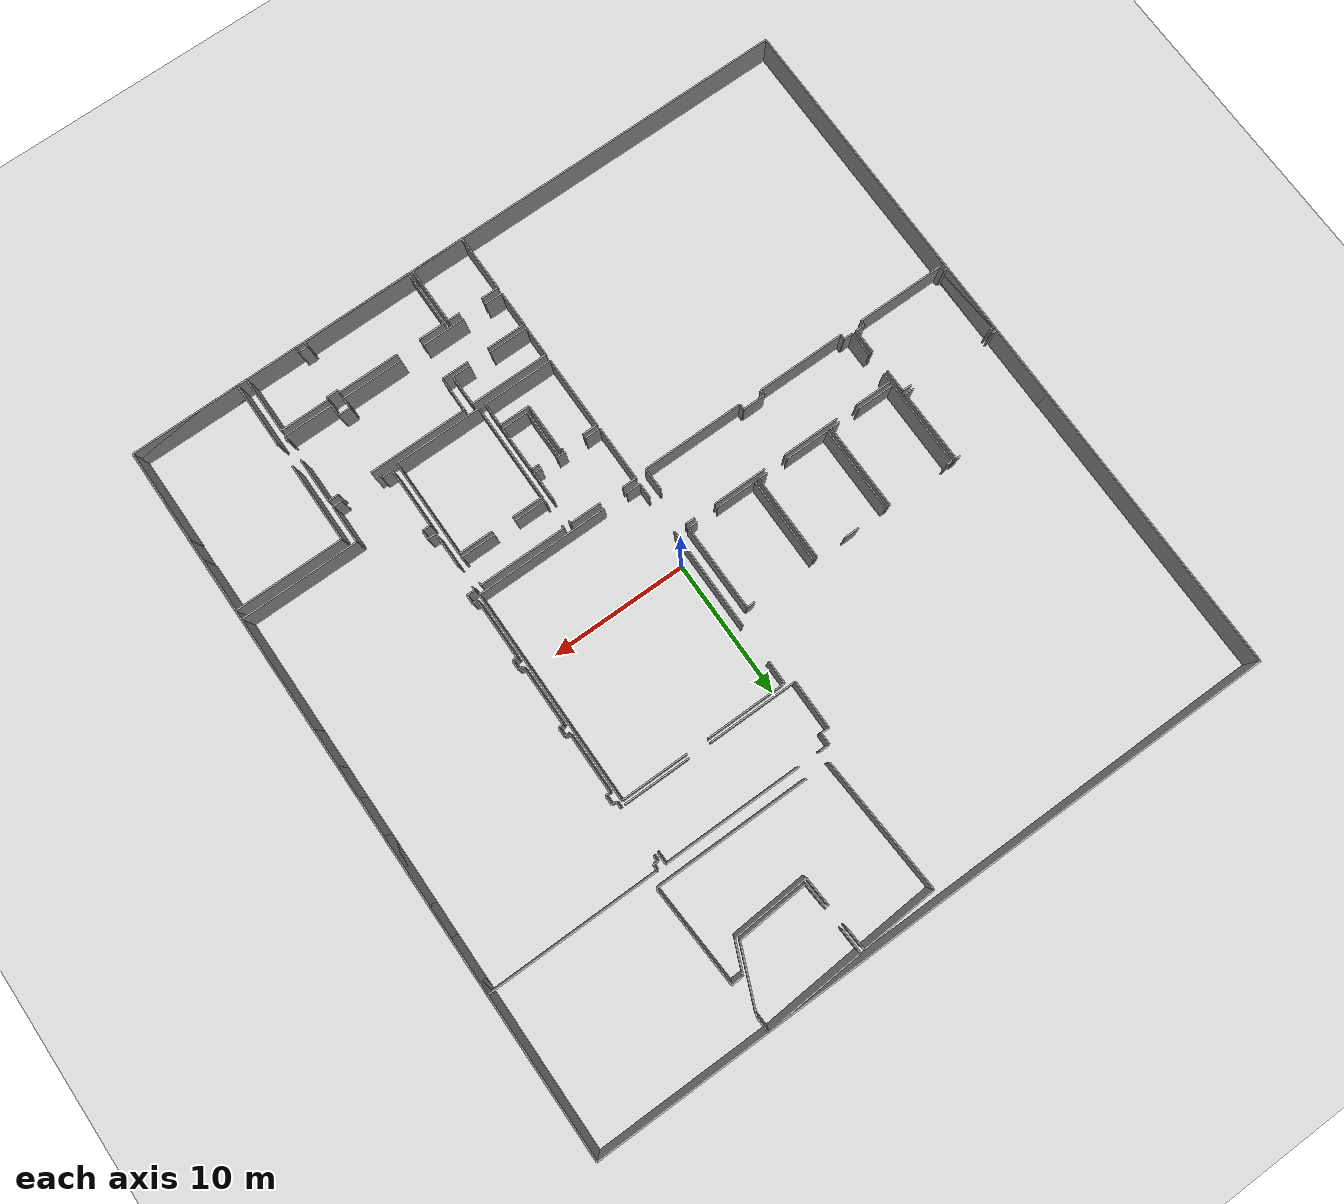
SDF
<sdf version="1.6">
  <world name="default">
    <light name="sun" type="directional">
      <cast_shadows>1</cast_shadows>
      <pose frame="">0 0 10 0 -0 0</pose>
      <diffuse>0.8 0.8 0.8 1</diffuse>
      <specular>0.1 0.1 0.1 1</specular>
      <attenuation>
        <range>1000</range>
        <constant>0.9</constant>
        <linear>0.01</linear>
        <quadratic>0.001</quadratic>
      </attenuation>
      <direction>-0.5 0.5 -1</direction>
    </light>
    <model name="ground_plane">
      <static>1</static>
      <link name="link">
        <collision name="collision">
          <geometry>
            <plane>
              <normal>0 0 1</normal>
              <size>100 100</size>
            </plane>
          </geometry>
          <surface>
            <friction>
              <ode>
                <mu>100</mu>
                <mu2>50</mu2>
              </ode>
              <torsional>
                <ode />
              </torsional>
            </friction>
            <contact>
              <ode />
            </contact>
            <bounce />
          </surface>
          <max_contacts>10</max_contacts>
        </collision>
        <visual name="visual">
          <cast_shadows>0</cast_shadows>
          <geometry>
            <plane>
              <normal>0 0 1</normal>
              <size>100 100</size>
            </plane>
          </geometry>
          <material>
            <script>
              <uri>file://media/materials/scripts/gazebo.material</uri>
              <name>Gazebo/Grey</name>
            </script>
          </material>
        </visual>
        <self_collide>0</self_collide>
        <kinematic>0</kinematic>
        <gravity>1</gravity>
      </link>
    </model>
    <gravity>0 0 -9.8</gravity>
    <magnetic_field>6e-06 2.3e-05 -4.2e-05</magnetic_field>
    <atmosphere type="adiabatic" />
    <physics default="0" name="default_physics" type="ode">
      <max_step_size>0.001</max_step_size>
      <real_time_factor>1</real_time_factor>
      <real_time_update_rate>1000</real_time_update_rate>
    </physics>
    <scene>
      <ambient>0.4 0.4 0.4 1</ambient>
      <background>0.7 0.7 0.7 1</background>
      <shadows>1</shadows>
    </scene>
    <spherical_coordinates>
      <surface_model>EARTH_WGS84</surface_model>
      <latitude_deg>0</latitude_deg>
      <longitude_deg>0</longitude_deg>
      <elevation>0</elevation>
      <heading_deg>0</heading_deg>
    </spherical_coordinates>
  <model name="50025630">
		<static>1</static>
		<link name="Wall_0">
			<collision name="Wall_0_Collision">
				<geometry>
					<box>
						<size>11.3128901363 0.1 2.5</size>
					</box>
				</geometry>
				<pose frame="">5.65644506817 0 1.25 0 0 0</pose>
			</collision>
			<visual name="Wall_0_Visual">
				<pose frame="">5.65644506817 0 1.25 0 0 0</pose>
				<geometry>
					<box>
						<size>11.3128901363 0.1 2.5</size>
					</box>
				</geometry>
				<material>
					<script>
						<uri>file://media/materials/scripts/gazebo.material</uri>
						<name>Gazebo/Grey</name>
					</script>
					<ambient>1 1 1 1</ambient>
				</material>
			</visual>
			<pose frame="">38.7109228649 -10.6291077427 0 0 0 3.14159265359</pose>
		</link>
		<link name="Wall_1">
			<collision name="Wall_1_Collision">
				<geometry>
					<box>
						<size>9.8324522599 0.1 2.5</size>
					</box>
				</geometry>
				<pose frame="">4.91622612995 0 1.25 0 0 0</pose>
			</collision>
			<visual name="Wall_1_Visual">
				<pose frame="">4.91622612995 0 1.25 0 0 0</pose>
				<geometry>
					<box>
						<size>9.8324522599 0.1 2.5</size>
					</box>
				</geometry>
				<material>
					<script>
						<uri>file://media/materials/scripts/gazebo.material</uri>
						<name>Gazebo/Grey</name>
					</script>
					<ambient>1 1 1 1</ambient>
				</material>
			</visual>
			<pose frame="">25.6572070842 -10.6291077427 0 0 0 1.63290090576</pose>
		</link>
		<link name="Wall_2">
			<collision name="Wall_2_Collision">
				<geometry>
					<box>
						<size>5.55154715457 0.1 2.5</size>
					</box>
				</geometry>
				<pose frame="">2.77577357729 0 1.25 0 0 0</pose>
			</collision>
			<visual name="Wall_2_Visual">
				<pose frame="">2.77577357729 0 1.25 0 0 0</pose>
				<geometry>
					<box>
						<size>5.55154715457 0.1 2.5</size>
					</box>
				</geometry>
				<material>
					<script>
						<uri>file://media/materials/scripts/gazebo.material</uri>
						<name>Gazebo/Grey</name>
					</script>
					<ambient>1 1 1 1</ambient>
				</material>
			</visual>
			<pose frame="">25.0469592385 -0.815611168615 0 0 0 0.0597673902472</pose>
		</link>
		<link name="Wall_3">
			<collision name="Wall_3_Collision">
				<geometry>
					<box>
						<size>1.67304815037 0.1 2.5</size>
					</box>
				</geometry>
				<pose frame="">0.836524075186 0 1.25 0 0 0</pose>
			</collision>
			<visual name="Wall_3_Visual">
				<pose frame="">0.836524075186 0 1.25 0 0 0</pose>
				<geometry>
					<box>
						<size>1.67304815037 0.1 2.5</size>
					</box>
				</geometry>
				<material>
					<script>
						<uri>file://media/materials/scripts/gazebo.material</uri>
						<name>Gazebo/Grey</name>
					</script>
					<ambient>1 1 1 1</ambient>
				</material>
			</visual>
			<pose frame="">30.5885938899 -0.484007188351 0 0 0 -1.50181448952</pose>
		</link>
		<link name="Wall_4">
			<collision name="Wall_4_Collision">
				<geometry>
					<box>
						<size>2.11933940147 0.1 2.5</size>
					</box>
				</geometry>
				<pose frame="">1.05966970073 0 1.25 0 0 0</pose>
			</collision>
			<visual name="Wall_4_Visual">
				<pose frame="">1.05966970073 0 1.25 0 0 0</pose>
				<geometry>
					<box>
						<size>2.11933940147 0.1 2.5</size>
					</box>
				</geometry>
				<material>
					<script>
						<uri>file://media/materials/scripts/gazebo.material</uri>
						<name>Gazebo/Grey</name>
					</script>
					<ambient>1 1 1 1</ambient>
				</material>
			</visual>
			<pose frame="">30.8034824133 -3.75216698311 0 0 0 -1.50477028506</pose>
		</link>
		<link name="Wall_5">
			<collision name="Wall_5_Collision">
				<geometry>
					<box>
						<size>5.61351934982 0.1 2.5</size>
					</box>
				</geometry>
				<pose frame="">2.80675967491 0 1.25 0 0 0</pose>
			</collision>
			<visual name="Wall_5_Visual">
				<pose frame="">2.80675967491 0 1.25 0 0 0</pose>
				<geometry>
					<box>
						<size>5.61351934982 0.1 2.5</size>
					</box>
				</geometry>
				<material>
					<script>
						<uri>file://media/materials/scripts/gazebo.material</uri>
						<name>Gazebo/Grey</name>
					</script>
					<ambient>1 1 1 1</ambient>
				</material>
			</visual>
			<pose frame="">30.9433123567 -5.866888498 0 0 0 0.0620307098715</pose>
		</link>
		<link name="Wall_6">
			<collision name="Wall_6_Collision">
				<geometry>
					<box>
						<size>2.22121321932 0.1 2.5</size>
					</box>
				</geometry>
				<pose frame="">1.11060660966 0 1.25 0 0 0</pose>
			</collision>
			<visual name="Wall_6_Visual">
				<pose frame="">1.11060660966 0 1.25 0 0 0</pose>
				<geometry>
					<box>
						<size>2.22121321932 0.1 2.5</size>
					</box>
				</geometry>
				<material>
					<script>
						<uri>file://media/materials/scripts/gazebo.material</uri>
						<name>Gazebo/Grey</name>
					</script>
					<ambient>1 1 1 1</ambient>
				</material>
			</visual>
			<pose frame="">36.546035294 -5.51890117287 0 0 0 1.16686553003</pose>
		</link>
		<link name="Wall_7">
			<collision name="Wall_7_Collision">
				<geometry>
					<box>
						<size>0.85191448878 0.1 2.5</size>
					</box>
				</geometry>
				<pose frame="">0.42595724439 0 1.25 0 0 0</pose>
			</collision>
			<visual name="Wall_7_Visual">
				<pose frame="">0.42595724439 0 1.25 0 0 0</pose>
				<geometry>
					<box>
						<size>0.85191448878 0.1 2.5</size>
					</box>
				</geometry>
				<material>
					<script>
						<uri>file://media/materials/scripts/gazebo.material</uri>
						<name>Gazebo/Grey</name>
					</script>
					<ambient>1 1 1 1</ambient>
				</material>
			</visual>
			<pose frame="">37.419051671 -3.47644417915 0 0 0 0.0451863527041</pose>
		</link>
		<link name="Wall_8">
			<collision name="Wall_8_Collision">
				<geometry>
					<box>
						<size>7.20464430718 0.1 2.5</size>
					</box>
				</geometry>
				<pose frame="">3.60232215359 0 1.25 0 0 0</pose>
			</collision>
			<visual name="Wall_8_Visual">
				<pose frame="">3.60232215359 0 1.25 0 0 0</pose>
				<geometry>
					<box>
						<size>7.20464430718 0.1 2.5</size>
					</box>
				</geometry>
				<material>
					<script>
						<uri>file://media/materials/scripts/gazebo.material</uri>
						<name>Gazebo/Grey</name>
					</script>
					<ambient>1 1 1 1</ambient>
				</material>
			</visual>
			<pose frame="">38.2700965855 -3.43796236911 0 0 0 -1.50957168</pose>
		</link>
		<link name="Wall_9">
			<collision name="Wall_9_Collision">
				<geometry>
					<box>
						<size>5.19604761874 0.1 2.5</size>
					</box>
				</geometry>
				<pose frame="">2.59802380937 0 1.25 0 0 0</pose>
			</collision>
			<visual name="Wall_9_Visual">
				<pose frame="">2.59802380937 0 1.25 0 0 0</pose>
				<geometry>
					<box>
						<size>5.19604761874 0.1 2.5</size>
					</box>
				</geometry>
				<material>
					<script>
						<uri>file://media/materials/scripts/gazebo.material</uri>
						<name>Gazebo/Grey</name>
					</script>
					<ambient>1 1 1 1</ambient>
				</material>
			</visual>
			<pose frame="">36.3642944684 -5.25092553198 0 0 0 -3.07346853266</pose>
		</link>
		<link name="Wall_10">
			<collision name="Wall_10_Collision">
				<geometry>
					<box>
						<size>1.88013856062 0.1 2.5</size>
					</box>
				</geometry>
				<pose frame="">0.940069280308 0 1.25 0 0 0</pose>
			</collision>
			<visual name="Wall_10_Visual">
				<pose frame="">0.940069280308 0 1.25 0 0 0</pose>
				<geometry>
					<box>
						<size>1.88013856062 0.1 2.5</size>
					</box>
				</geometry>
				<material>
					<script>
						<uri>file://media/materials/scripts/gazebo.material</uri>
						<name>Gazebo/Grey</name>
					</script>
					<ambient>1 1 1 1</ambient>
				</material>
			</visual>
			<pose frame="">31.1802993453 -5.60462797742 0 0 0 1.64144444996</pose>
		</link>
		<link name="Wall_11">
			<collision name="Wall_11_Collision">
				<geometry>
					<box>
						<size>1.65555187292 0.1 2.5</size>
					</box>
				</geometry>
				<pose frame="">0.827775936462 0 1.25 0 0 0</pose>
			</collision>
			<visual name="Wall_11_Visual">
				<pose frame="">0.827775936462 0 1.25 0 0 0</pose>
				<geometry>
					<box>
						<size>1.65555187292 0.1 2.5</size>
					</box>
				</geometry>
				<material>
					<script>
						<uri>file://media/materials/scripts/gazebo.material</uri>
						<name>Gazebo/Grey</name>
					</script>
					<ambient>1 1 1 1</ambient>
				</material>
			</visual>
			<pose frame="">30.9783650946 -2.10329127428 0 0 0 1.6212182583</pose>
		</link>
		<link name="Wall_12">
			<collision name="Wall_12_Collision">
				<geometry>
					<box>
						<size>7.18796307105 0.1 2.5</size>
					</box>
				</geometry>
				<pose frame="">3.59398153552 0 1.25 0 0 0</pose>
			</collision>
			<visual name="Wall_12_Visual">
				<pose frame="">3.59398153552 0 1.25 0 0 0</pose>
				<geometry>
					<box>
						<size>7.18796307105 0.1 2.5</size>
					</box>
				</geometry>
				<material>
					<script>
						<uri>file://media/materials/scripts/gazebo.material</uri>
						<name>Gazebo/Grey</name>
					</script>
					<ambient>1 1 1 1</ambient>
				</material>
			</visual>
			<pose frame="">30.8949243382 -0.449843469205 0 0 0 0.0626238097837</pose>
		</link>
		<link name="Wall_13">
			<collision name="Wall_13_Collision">
				<geometry>
					<box>
						<size>1.10530514953 0.1 2.5</size>
					</box>
				</geometry>
				<pose frame="">0.552652574765 0 1.25 0 0 0</pose>
			</collision>
			<visual name="Wall_13_Visual">
				<pose frame="">0.552652574765 0 1.25 0 0 0</pose>
				<geometry>
					<box>
						<size>1.10530514953 0.1 2.5</size>
					</box>
				</geometry>
				<material>
					<script>
						<uri>file://media/materials/scripts/gazebo.material</uri>
						<name>Gazebo/Grey</name>
					</script>
					<ambient>1 1 1 1</ambient>
				</material>
			</visual>
			<pose frame="">38.0687973482 -0.0 0 0 0 -1.51826157845</pose>
		</link>
		<link name="Wall_14">
			<collision name="Wall_14_Collision">
				<geometry>
					<box>
						<size>4.50614827792 0.1 2.5</size>
					</box>
				</geometry>
				<pose frame="">2.25307413896 0 1.25 0 0 0</pose>
			</collision>
			<visual name="Wall_14_Visual">
				<pose frame="">2.25307413896 0 1.25 0 0 0</pose>
				<geometry>
					<box>
						<size>4.50614827792 0.1 2.5</size>
					</box>
				</geometry>
				<material>
					<script>
						<uri>file://media/materials/scripts/gazebo.material</uri>
						<name>Gazebo/Grey</name>
					</script>
					<ambient>1 1 1 1</ambient>
				</material>
			</visual>
			<pose frame="">38.1268375699 -1.10378023457 0 0 0 -1.97266827118</pose>
		</link>
		<link name="Wall_15">
			<collision name="Wall_15_Collision">
				<geometry>
					<box>
						<size>4.88731687802 0.1 2.5</size>
					</box>
				</geometry>
				<pose frame="">2.44365843901 0 1.25 0 0 0</pose>
			</collision>
			<visual name="Wall_15_Visual">
				<pose frame="">2.44365843901 0 1.25 0 0 0</pose>
				<geometry>
					<box>
						<size>4.88731687802 0.1 2.5</size>
					</box>
				</geometry>
				<material>
					<script>
						<uri>file://media/materials/scripts/gazebo.material</uri>
						<name>Gazebo/Grey</name>
					</script>
					<ambient>1 1 1 1</ambient>
				</material>
			</visual>
			<pose frame="">37.4187976657 -15.8639039352 0 0 0 3.14159265359</pose>
		</link>
		<link name="Wall_16">
			<collision name="Wall_16_Collision">
				<geometry>
					<box>
						<size>6.50520393454 0.1 2.5</size>
					</box>
				</geometry>
				<pose frame="">3.25260196727 0 1.25 0 0 0</pose>
			</collision>
			<visual name="Wall_16_Visual">
				<pose frame="">3.25260196727 0 1.25 0 0 0</pose>
				<geometry>
					<box>
						<size>6.50520393454 0.1 2.5</size>
					</box>
				</geometry>
				<material>
					<script>
						<uri>file://media/materials/scripts/gazebo.material</uri>
						<name>Gazebo/Grey</name>
					</script>
					<ambient>1 1 1 1</ambient>
				</material>
			</visual>
			<pose frame="">30.9283260413 -15.8639039352 0 0 0 3.14159265359</pose>
		</link>
		<link name="Wall_17">
			<collision name="Wall_17_Collision">
				<geometry>
					<box>
						<size>3.53105532871 0.1 2.5</size>
					</box>
				</geometry>
				<pose frame="">1.76552766436 0 1.25 0 0 0</pose>
			</collision>
			<visual name="Wall_17_Visual">
				<pose frame="">1.76552766436 0 1.25 0 0 0</pose>
				<geometry>
					<box>
						<size>3.53105532871 0.1 2.5</size>
					</box>
				</geometry>
				<material>
					<script>
						<uri>file://media/materials/scripts/gazebo.material</uri>
						<name>Gazebo/Grey</name>
					</script>
					<ambient>1 1 1 1</ambient>
				</material>
			</visual>
			<pose frame="">24.4231221067 -15.8639039352 0 0 0 1.57079632679</pose>
		</link>
		<link name="Wall_18">
			<collision name="Wall_18_Collision">
				<geometry>
					<box>
						<size>0.581418238854 0.1 2.5</size>
					</box>
				</geometry>
				<pose frame="">0.290709119427 0 1.25 0 0 0</pose>
			</collision>
			<visual name="Wall_18_Visual">
				<pose frame="">0.290709119427 0 1.25 0 0 0</pose>
				<geometry>
					<box>
						<size>0.581418238854 0.1 2.5</size>
					</box>
				</geometry>
				<material>
					<script>
						<uri>file://media/materials/scripts/gazebo.material</uri>
						<name>Gazebo/Grey</name>
					</script>
					<ambient>1 1 1 1</ambient>
				</material>
			</visual>
			<pose frame="">24.4231221067 -12.3328486065 0 0 0 0.0</pose>
		</link>
		<link name="Wall_19">
			<collision name="Wall_19_Collision">
				<geometry>
					<box>
						<size>0.856506029452 0.1 2.5</size>
					</box>
				</geometry>
				<pose frame="">0.428253014726 0 1.25 0 0 0</pose>
			</collision>
			<visual name="Wall_19_Visual">
				<pose frame="">0.428253014726 0 1.25 0 0 0</pose>
				<geometry>
					<box>
						<size>0.856506029452 0.1 2.5</size>
					</box>
				</geometry>
				<material>
					<script>
						<uri>file://media/materials/scripts/gazebo.material</uri>
						<name>Gazebo/Grey</name>
					</script>
					<ambient>1 1 1 1</ambient>
				</material>
			</visual>
			<pose frame="">25.0045403456 -12.3328486065 0 0 0 1.57079632679</pose>
		</link>
		<link name="Wall_20">
			<collision name="Wall_20_Collision">
				<geometry>
					<box>
						<size>0.713882027217 0.1 2.5</size>
					</box>
				</geometry>
				<pose frame="">0.356941013608 0 1.25 0 0 0</pose>
			</collision>
			<visual name="Wall_20_Visual">
				<pose frame="">0.356941013608 0 1.25 0 0 0</pose>
				<geometry>
					<box>
						<size>0.713882027217 0.1 2.5</size>
					</box>
				</geometry>
				<material>
					<script>
						<uri>file://media/materials/scripts/gazebo.material</uri>
						<name>Gazebo/Grey</name>
					</script>
					<ambient>1 1 1 1</ambient>
				</material>
			</visual>
			<pose frame="">25.0045403456 -11.476342577 0 0 0 0.0</pose>
		</link>
		<link name="Wall_21">
			<collision name="Wall_21_Collision">
				<geometry>
					<box>
						<size>10.0843932765 0.1 2.5</size>
					</box>
				</geometry>
				<pose frame="">5.04219663824 0 1.25 0 0 0</pose>
			</collision>
			<visual name="Wall_21_Visual">
				<pose frame="">5.04219663824 0 1.25 0 0 0</pose>
				<geometry>
					<box>
						<size>10.0843932765 0.1 2.5</size>
					</box>
				</geometry>
				<material>
					<script>
						<uri>file://media/materials/scripts/gazebo.material</uri>
						<name>Gazebo/Grey</name>
					</script>
					<ambient>1 1 1 1</ambient>
				</material>
			</visual>
			<pose frame="">27.3217041219 -11.476342577 0 0 0 0.0</pose>
		</link>
		<link name="Wall_22">
			<collision name="Wall_22_Collision">
				<geometry>
					<box>
						<size>0.875775525954 0.1 2.5</size>
					</box>
				</geometry>
				<pose frame="">0.437887762977 0 1.25 0 0 0</pose>
			</collision>
			<visual name="Wall_22_Visual">
				<pose frame="">0.437887762977 0 1.25 0 0 0</pose>
				<geometry>
					<box>
						<size>0.875775525954 0.1 2.5</size>
					</box>
				</geometry>
				<material>
					<script>
						<uri>file://media/materials/scripts/gazebo.material</uri>
						<name>Gazebo/Grey</name>
					</script>
					<ambient>1 1 1 1</ambient>
				</material>
			</visual>
			<pose frame="">37.4060973984 -11.476342577 0 0 0 -1.55629408033</pose>
		</link>
		<link name="Wall_23">
			<collision name="Wall_23_Collision">
				<geometry>
					<box>
						<size>9.59695701595 0.1 2.5</size>
					</box>
				</geometry>
				<pose frame="">4.79847850797 0 1.25 0 0 0</pose>
			</collision>
			<visual name="Wall_23_Visual">
				<pose frame="">4.79847850797 0 1.25 0 0 0</pose>
				<geometry>
					<box>
						<size>9.59695701595 0.1 2.5</size>
					</box>
				</geometry>
				<material>
					<script>
						<uri>file://media/materials/scripts/gazebo.material</uri>
						<name>Gazebo/Grey</name>
					</script>
					<ambient>1 1 1 1</ambient>
				</material>
			</visual>
			<pose frame="">37.4077484331 -31.8441423192 0 0 0 3.14159265359</pose>
		</link>
		<link name="Wall_24">
			<collision name="Wall_24_Collision">
				<geometry>
					<box>
						<size>1.0602183176 0.1 2.5</size>
					</box>
				</geometry>
				<pose frame="">0.530109158798 0 1.25 0 0 0</pose>
			</collision>
			<visual name="Wall_24_Visual">
				<pose frame="">0.530109158798 0 1.25 0 0 0</pose>
				<geometry>
					<box>
						<size>1.0602183176 0.1 2.5</size>
					</box>
				</geometry>
				<material>
					<script>
						<uri>file://media/materials/scripts/gazebo.material</uri>
						<name>Gazebo/Grey</name>
					</script>
					<ambient>1 1 1 1</ambient>
				</material>
			</visual>
			<pose frame="">26.0802529893 -31.8441423192 0 0 0 3.14159265359</pose>
		</link>
		<link name="Wall_25">
			<collision name="Wall_25_Collision">
				<geometry>
					<box>
						<size>1.07317259028 0.1 2.5</size>
					</box>
				</geometry>
				<pose frame="">0.536586295142 0 1.25 0 0 0</pose>
			</collision>
			<visual name="Wall_25_Visual">
				<pose frame="">0.536586295142 0 1.25 0 0 0</pose>
				<geometry>
					<box>
						<size>1.07317259028 0.1 2.5</size>
					</box>
				</geometry>
				<material>
					<script>
						<uri>file://media/materials/scripts/gazebo.material</uri>
						<name>Gazebo/Grey</name>
					</script>
					<ambient>1 1 1 1</ambient>
				</material>
			</visual>
			<pose frame="">25.0200346717 -31.8441423192 0 0 0 1.57079632679</pose>
		</link>
		<link name="Wall_26">
			<collision name="Wall_26_Collision">
				<geometry>
					<box>
						<size>7.44070562685 0.1 2.5</size>
					</box>
				</geometry>
				<pose frame="">3.72035281343 0 1.25 0 0 0</pose>
			</collision>
			<visual name="Wall_26_Visual">
				<pose frame="">3.72035281343 0 1.25 0 0 0</pose>
				<geometry>
					<box>
						<size>7.44070562685 0.1 2.5</size>
					</box>
				</geometry>
				<material>
					<script>
						<uri>file://media/materials/scripts/gazebo.material</uri>
						<name>Gazebo/Grey</name>
					</script>
					<ambient>1 1 1 1</ambient>
				</material>
			</visual>
			<pose frame="">25.0200346717 -28.034062117 0 0 0 1.57079632679</pose>
		</link>
		<link name="Wall_27">
			<collision name="Wall_27_Collision">
				<geometry>
					<box>
						<size>1.68469046273 0.1 2.5</size>
					</box>
				</geometry>
				<pose frame="">0.842345231367 0 1.25 0 0 0</pose>
			</collision>
			<visual name="Wall_27_Visual">
				<pose frame="">0.842345231367 0 1.25 0 0 0</pose>
				<geometry>
					<box>
						<size>1.68469046273 0.1 2.5</size>
					</box>
				</geometry>
				<material>
					<script>
						<uri>file://media/materials/scripts/gazebo.material</uri>
						<name>Gazebo/Grey</name>
					</script>
					<ambient>1 1 1 1</ambient>
				</material>
			</visual>
			<pose frame="">25.0200346717 -17.8413355601 0 0 0 1.57079632679</pose>
		</link>
		<link name="Wall_28">
			<collision name="Wall_28_Collision">
				<geometry>
					<box>
						<size>5.89622611556 0.1 2.5</size>
					</box>
				</geometry>
				<pose frame="">2.94811305778 0 1.25 0 0 0</pose>
			</collision>
			<visual name="Wall_28_Visual">
				<pose frame="">2.94811305778 0 1.25 0 0 0</pose>
				<geometry>
					<box>
						<size>5.89622611556 0.1 2.5</size>
					</box>
				</geometry>
				<material>
					<script>
						<uri>file://media/materials/scripts/gazebo.material</uri>
						<name>Gazebo/Grey</name>
					</script>
					<ambient>1 1 1 1</ambient>
				</material>
			</visual>
			<pose frame="">25.0200346717 -16.1566450974 0 0 0 0.0</pose>
		</link>
		<link name="Wall_29">
			<collision name="Wall_29_Collision">
				<geometry>
					<box>
						<size>4.92617969608 0.1 2.5</size>
					</box>
				</geometry>
				<pose frame="">2.46308984804 0 1.25 0 0 0</pose>
			</collision>
			<visual name="Wall_29_Visual">
				<pose frame="">2.46308984804 0 1.25 0 0 0</pose>
				<geometry>
					<box>
						<size>4.92617969608 0.1 2.5</size>
					</box>
				</geometry>
				<material>
					<script>
						<uri>file://media/materials/scripts/gazebo.material</uri>
						<name>Gazebo/Grey</name>
					</script>
					<ambient>1 1 1 1</ambient>
				</material>
			</visual>
			<pose frame="">32.4822037504 -16.1566450974 0 0 0 0.0</pose>
		</link>
		<link name="Wall_30">
			<collision name="Wall_30_Collision">
				<geometry>
					<box>
						<size>15.6874972347 0.1 2.5</size>
					</box>
				</geometry>
				<pose frame="">7.84374861733 0 1.25 0 0 0</pose>
			</collision>
			<visual name="Wall_30_Visual">
				<pose frame="">7.84374861733 0 1.25 0 0 0</pose>
				<geometry>
					<box>
						<size>15.6874972347 0.1 2.5</size>
					</box>
				</geometry>
				<material>
					<script>
						<uri>file://media/materials/scripts/gazebo.material</uri>
						<name>Gazebo/Grey</name>
					</script>
					<ambient>1 1 1 1</ambient>
				</material>
			</visual>
			<pose frame="">37.4083834465 -16.1566450974 0 0 0 -1.57083680574</pose>
		</link>
		<link name="Wall_31">
			<collision name="Wall_31_Collision">
				<geometry>
					<box>
						<size>8.59820799228 0.1 2.5</size>
					</box>
				</geometry>
				<pose frame="">4.29910399614 0 1.25 0 0 0</pose>
			</collision>
			<visual name="Wall_31_Visual">
				<pose frame="">4.29910399614 0 1.25 0 0 0</pose>
				<geometry>
					<box>
						<size>8.59820799228 0.1 2.5</size>
					</box>
				</geometry>
				<material>
					<script>
						<uri>file://media/materials/scripts/gazebo.material</uri>
						<name>Gazebo/Grey</name>
					</script>
					<ambient>1 1 1 1</ambient>
				</material>
			</visual>
			<pose frame="">50.4575271309 -39.2135994463 0 0 0 3.14159265359</pose>
		</link>
		<link name="Wall_32">
			<collision name="Wall_32_Collision">
				<geometry>
					<box>
						<size>2.80104396198 0.1 2.5</size>
					</box>
				</geometry>
				<pose frame="">1.40052198099 0 1.25 0 0 0</pose>
			</collision>
			<visual name="Wall_32_Visual">
				<pose frame="">1.40052198099 0 1.25 0 0 0</pose>
				<geometry>
					<box>
						<size>2.80104396198 0.1 2.5</size>
					</box>
				</geometry>
				<material>
					<script>
						<uri>file://media/materials/scripts/gazebo.material</uri>
						<name>Gazebo/Grey</name>
					</script>
					<ambient>1 1 1 1</ambient>
				</material>
			</visual>
			<pose frame="">41.8593191387 -39.2135994463 0 0 0 -1.57079632679</pose>
		</link>
		<link name="Wall_33">
			<collision name="Wall_33_Collision">
				<geometry>
					<box>
						<size>0.660794909733 0.1 2.5</size>
					</box>
				</geometry>
				<pose frame="">0.330397454866 0 1.25 0 0 0</pose>
			</collision>
			<visual name="Wall_33_Visual">
				<pose frame="">0.330397454866 0 1.25 0 0 0</pose>
				<geometry>
					<box>
						<size>0.660794909733 0.1 2.5</size>
					</box>
				</geometry>
				<material>
					<script>
						<uri>file://media/materials/scripts/gazebo.material</uri>
						<name>Gazebo/Grey</name>
					</script>
					<ambient>1 1 1 1</ambient>
				</material>
			</visual>
			<pose frame="">41.8593191387 -42.0146434082 0 0 0 3.14159265359</pose>
		</link>
		<link name="Wall_34">
			<collision name="Wall_34_Collision">
				<geometry>
					<box>
						<size>0.40082043727 0.1 2.5</size>
					</box>
				</geometry>
				<pose frame="">0.200410218635 0 1.25 0 0 0</pose>
			</collision>
			<visual name="Wall_34_Visual">
				<pose frame="">0.200410218635 0 1.25 0 0 0</pose>
				<geometry>
					<box>
						<size>0.40082043727 0.1 2.5</size>
					</box>
				</geometry>
				<material>
					<script>
						<uri>file://media/materials/scripts/gazebo.material</uri>
						<name>Gazebo/Grey</name>
					</script>
					<ambient>1 1 1 1</ambient>
				</material>
			</visual>
			<pose frame="">38.6610108143 -42.0146434082 0 0 0 3.14159265359</pose>
		</link>
		<link name="Wall_35">
			<collision name="Wall_35_Collision">
				<geometry>
					<box>
						<size>0.204093296164 0.1 2.5</size>
					</box>
				</geometry>
				<pose frame="">0.102046648082 0 1.25 0 0 0</pose>
			</collision>
			<visual name="Wall_35_Visual">
				<pose frame="">0.102046648082 0 1.25 0 0 0</pose>
				<geometry>
					<box>
						<size>0.204093296164 0.1 2.5</size>
					</box>
				</geometry>
				<material>
					<script>
						<uri>file://media/materials/scripts/gazebo.material</uri>
						<name>Gazebo/Grey</name>
					</script>
					<ambient>1 1 1 1</ambient>
				</material>
			</visual>
			<pose frame="">38.260190377 -42.0146434082 0 0 0 1.57079632679</pose>
		</link>
		<link name="Wall_36">
			<collision name="Wall_36_Collision">
				<geometry>
					<box>
						<size>0.793385700769 0.1 2.5</size>
					</box>
				</geometry>
				<pose frame="">0.396692850385 0 1.25 0 0 0</pose>
			</collision>
			<visual name="Wall_36_Visual">
				<pose frame="">0.396692850385 0 1.25 0 0 0</pose>
				<geometry>
					<box>
						<size>0.793385700769 0.1 2.5</size>
					</box>
				</geometry>
				<material>
					<script>
						<uri>file://media/materials/scripts/gazebo.material</uri>
						<name>Gazebo/Grey</name>
					</script>
					<ambient>1 1 1 1</ambient>
				</material>
			</visual>
			<pose frame="">38.260190377 -41.8105501121 0 0 0 3.14159265359</pose>
		</link>
		<link name="Wall_37">
			<collision name="Wall_37_Collision">
				<geometry>
					<box>
						<size>4.43163128584 0.1 2.5</size>
					</box>
				</geometry>
				<pose frame="">2.21581564292 0 1.25 0 0 0</pose>
			</collision>
			<visual name="Wall_37_Visual">
				<pose frame="">2.21581564292 0 1.25 0 0 0</pose>
				<geometry>
					<box>
						<size>4.43163128584 0.1 2.5</size>
					</box>
				</geometry>
				<material>
					<script>
						<uri>file://media/materials/scripts/gazebo.material</uri>
						<name>Gazebo/Grey</name>
					</script>
					<ambient>1 1 1 1</ambient>
				</material>
			</visual>
			<pose frame="">37.4668046762 -41.8105501121 0 0 0 1.57079632679</pose>
		</link>
		<link name="Wall_38">
			<collision name="Wall_38_Collision">
				<geometry>
					<box>
						<size>0.608215802943 0.1 2.5</size>
					</box>
				</geometry>
				<pose frame="">0.304107901471 0 1.25 0 0 0</pose>
			</collision>
			<visual name="Wall_38_Visual">
				<pose frame="">0.304107901471 0 1.25 0 0 0</pose>
				<geometry>
					<box>
						<size>0.608215802943 0.1 2.5</size>
					</box>
				</geometry>
				<material>
					<script>
						<uri>file://media/materials/scripts/gazebo.material</uri>
						<name>Gazebo/Grey</name>
					</script>
					<ambient>1 1 1 1</ambient>
				</material>
			</visual>
			<pose frame="">37.4668046762 -37.3789188262 0 0 0 0.0</pose>
		</link>
		<link name="Wall_39">
			<collision name="Wall_39_Collision">
				<geometry>
					<box>
						<size>0.654063768042 0.1 2.5</size>
					</box>
				</geometry>
				<pose frame="">0.327031884021 0 1.25 0 0 0</pose>
			</collision>
			<visual name="Wall_39_Visual">
				<pose frame="">0.327031884021 0 1.25 0 0 0</pose>
				<geometry>
					<box>
						<size>0.654063768042 0.1 2.5</size>
					</box>
				</geometry>
				<material>
					<script>
						<uri>file://media/materials/scripts/gazebo.material</uri>
						<name>Gazebo/Grey</name>
					</script>
					<ambient>1 1 1 1</ambient>
				</material>
			</visual>
			<pose frame="">38.0750204792 -37.3789188262 0 0 0 1.57079632679</pose>
		</link>
		<link name="Wall_40">
			<collision name="Wall_40_Collision">
				<geometry>
					<box>
						<size>0.596785562336 0.1 2.5</size>
					</box>
				</geometry>
				<pose frame="">0.298392781168 0 1.25 0 0 0</pose>
			</collision>
			<visual name="Wall_40_Visual">
				<pose frame="">0.298392781168 0 1.25 0 0 0</pose>
				<geometry>
					<box>
						<size>0.596785562336 0.1 2.5</size>
					</box>
				</geometry>
				<material>
					<script>
						<uri>file://media/materials/scripts/gazebo.material</uri>
						<name>Gazebo/Grey</name>
					</script>
					<ambient>1 1 1 1</ambient>
				</material>
			</visual>
			<pose frame="">38.0750204792 -36.7248550582 0 0 0 3.14159265359</pose>
		</link>
		<link name="Wall_41">
			<collision name="Wall_41_Collision">
				<geometry>
					<box>
						<size>2.52811521683 0.1 2.5</size>
					</box>
				</geometry>
				<pose frame="">1.26405760841 0 1.25 0 0 0</pose>
			</collision>
			<visual name="Wall_41_Visual">
				<pose frame="">1.26405760841 0 1.25 0 0 0</pose>
				<geometry>
					<box>
						<size>2.52811521683 0.1 2.5</size>
					</box>
				</geometry>
				<material>
					<script>
						<uri>file://media/materials/scripts/gazebo.material</uri>
						<name>Gazebo/Grey</name>
					</script>
					<ambient>1 1 1 1</ambient>
				</material>
			</visual>
			<pose frame="">37.4782349168 -36.7248550582 0 0 0 1.57079632679</pose>
		</link>
		<link name="Wall_42">
			<collision name="Wall_42_Collision">
				<geometry>
					<box>
						<size>0.315220635394 0.1 2.5</size>
					</box>
				</geometry>
				<pose frame="">0.157610317697 0 1.25 0 0 0</pose>
			</collision>
			<visual name="Wall_42_Visual">
				<pose frame="">0.157610317697 0 1.25 0 0 0</pose>
				<geometry>
					<box>
						<size>0.315220635394 0.1 2.5</size>
					</box>
				</geometry>
				<material>
					<script>
						<uri>file://media/materials/scripts/gazebo.material</uri>
						<name>Gazebo/Grey</name>
					</script>
					<ambient>1 1 1 1</ambient>
				</material>
			</visual>
			<pose frame="">37.4782349168 -32.5901560228 0 0 0 1.57079632679</pose>
		</link>
		<link name="Wall_43">
			<collision name="Wall_43_Collision">
				<geometry>
					<box>
						<size>0.582434260241 0.1 2.5</size>
					</box>
				</geometry>
				<pose frame="">0.291217130121 0 1.25 0 0 0</pose>
			</collision>
			<visual name="Wall_43_Visual">
				<pose frame="">0.291217130121 0 1.25 0 0 0</pose>
				<geometry>
					<box>
						<size>0.582434260241 0.1 2.5</size>
					</box>
				</geometry>
				<material>
					<script>
						<uri>file://media/materials/scripts/gazebo.material</uri>
						<name>Gazebo/Grey</name>
					</script>
					<ambient>1 1 1 1</ambient>
				</material>
			</visual>
			<pose frame="">37.4782349168 -32.2749353874 0 0 0 0.0</pose>
		</link>
		<link name="Wall_44">
			<collision name="Wall_44_Collision">
				<geometry>
					<box>
						<size>0.649237666453 0.1 2.5</size>
					</box>
				</geometry>
				<pose frame="">0.324618833226 0 1.25 0 0 0</pose>
			</collision>
			<visual name="Wall_44_Visual">
				<pose frame="">0.324618833226 0 1.25 0 0 0</pose>
				<geometry>
					<box>
						<size>0.649237666453 0.1 2.5</size>
					</box>
				</geometry>
				<material>
					<script>
						<uri>file://media/materials/scripts/gazebo.material</uri>
						<name>Gazebo/Grey</name>
					</script>
					<ambient>1 1 1 1</ambient>
				</material>
			</visual>
			<pose frame="">38.0606691771 -32.2749353874 0 0 0 1.57079632679</pose>
		</link>
		<link name="Wall_45">
			<collision name="Wall_45_Collision">
				<geometry>
					<box>
						<size>0.348495335827 0.1 2.5</size>
					</box>
				</geometry>
				<pose frame="">0.174247667913 0 1.25 0 0 0</pose>
			</collision>
			<visual name="Wall_45_Visual">
				<pose frame="">0.174247667913 0 1.25 0 0 0</pose>
				<geometry>
					<box>
						<size>0.348495335827 0.1 2.5</size>
					</box>
				</geometry>
				<material>
					<script>
						<uri>file://media/materials/scripts/gazebo.material</uri>
						<name>Gazebo/Grey</name>
					</script>
					<ambient>1 1 1 1</ambient>
				</material>
			</visual>
			<pose frame="">38.0606691771 -31.6256977209 0 0 0 3.14159265359</pose>
		</link>
		<link name="Wall_46">
			<collision name="Wall_46_Collision">
				<geometry>
					<box>
						<size>4.43506035802 0.1 2.5</size>
					</box>
				</geometry>
				<pose frame="">2.21753017901 0 1.25 0 0 0</pose>
			</collision>
			<visual name="Wall_46_Visual">
				<pose frame="">2.21753017901 0 1.25 0 0 0</pose>
				<geometry>
					<box>
						<size>4.43506035802 0.1 2.5</size>
					</box>
				</geometry>
				<material>
					<script>
						<uri>file://media/materials/scripts/gazebo.material</uri>
						<name>Gazebo/Grey</name>
					</script>
					<ambient>1 1 1 1</ambient>
				</material>
			</visual>
			<pose frame="">37.7121738413 -31.6256977209 0 0 0 1.57079632679</pose>
		</link>
		<link name="Wall_47">
			<collision name="Wall_47_Collision">
				<geometry>
					<box>
						<size>0.338335121954 0.1 2.5</size>
					</box>
				</geometry>
				<pose frame="">0.169167560977 0 1.25 0 0 0</pose>
			</collision>
			<visual name="Wall_47_Visual">
				<pose frame="">0.169167560977 0 1.25 0 0 0</pose>
				<geometry>
					<box>
						<size>0.338335121954 0.1 2.5</size>
					</box>
				</geometry>
				<material>
					<script>
						<uri>file://media/materials/scripts/gazebo.material</uri>
						<name>Gazebo/Grey</name>
					</script>
					<ambient>1 1 1 1</ambient>
				</material>
			</visual>
			<pose frame="">37.7121738413 -27.1906373629 0 0 0 0.0</pose>
		</link>
		<link name="Wall_48">
			<collision name="Wall_48_Collision">
				<geometry>
					<box>
						<size>0.669939102218 0.1 2.5</size>
					</box>
				</geometry>
				<pose frame="">0.334969551109 0 1.25 0 0 0</pose>
			</collision>
			<visual name="Wall_48_Visual">
				<pose frame="">0.334969551109 0 1.25 0 0 0</pose>
				<geometry>
					<box>
						<size>0.669939102218 0.1 2.5</size>
					</box>
				</geometry>
				<material>
					<script>
						<uri>file://media/materials/scripts/gazebo.material</uri>
						<name>Gazebo/Grey</name>
					</script>
					<ambient>1 1 1 1</ambient>
				</material>
			</visual>
			<pose frame="">38.0505089632 -27.1906373629 0 0 0 1.57079632679</pose>
		</link>
		<link name="Wall_49">
			<collision name="Wall_49_Collision">
				<geometry>
					<box>
						<size>0.335033052446 0.1 2.5</size>
					</box>
				</geometry>
				<pose frame="">0.167516526223 0 1.25 0 0 0</pose>
			</collision>
			<visual name="Wall_49_Visual">
				<pose frame="">0.167516526223 0 1.25 0 0 0</pose>
				<geometry>
					<box>
						<size>0.335033052446 0.1 2.5</size>
					</box>
				</geometry>
				<material>
					<script>
						<uri>file://media/materials/scripts/gazebo.material</uri>
						<name>Gazebo/Grey</name>
					</script>
					<ambient>1 1 1 1</ambient>
				</material>
			</visual>
			<pose frame="">38.0505089632 -26.5206982607 0 0 0 3.14159265359</pose>
		</link>
		<link name="Wall_50">
			<collision name="Wall_50_Collision">
				<geometry>
					<box>
						<size>4.43645738743 0.1 2.5</size>
					</box>
				</geometry>
				<pose frame="">2.21822869371 0 1.25 0 0 0</pose>
			</collision>
			<visual name="Wall_50_Visual">
				<pose frame="">2.21822869371 0 1.25 0 0 0</pose>
				<geometry>
					<box>
						<size>4.43645738743 0.1 2.5</size>
					</box>
				</geometry>
				<material>
					<script>
						<uri>file://media/materials/scripts/gazebo.material</uri>
						<name>Gazebo/Grey</name>
					</script>
					<ambient>1 1 1 1</ambient>
				</material>
			</visual>
			<pose frame="">37.7154759108 -26.5206982607 0 0 0 1.57079632679</pose>
		</link>
		<link name="Wall_51">
			<collision name="Wall_51_Collision">
				<geometry>
					<box>
						<size>0.345955282359 0.1 2.5</size>
					</box>
				</geometry>
				<pose frame="">0.172977641179 0 1.25 0 0 0</pose>
			</collision>
			<visual name="Wall_51_Visual">
				<pose frame="">0.172977641179 0 1.25 0 0 0</pose>
				<geometry>
					<box>
						<size>0.345955282359 0.1 2.5</size>
					</box>
				</geometry>
				<material>
					<script>
						<uri>file://media/materials/scripts/gazebo.material</uri>
						<name>Gazebo/Grey</name>
					</script>
					<ambient>1 1 1 1</ambient>
				</material>
			</visual>
			<pose frame="">37.7154759108 -22.0842408733 0 0 0 0.0</pose>
		</link>
		<link name="Wall_52">
			<collision name="Wall_52_Collision">
				<geometry>
					<box>
						<size>0.653301752002 0.1 2.5</size>
					</box>
				</geometry>
				<pose frame="">0.326650876001 0 1.25 0 0 0</pose>
			</collision>
			<visual name="Wall_52_Visual">
				<pose frame="">0.326650876001 0 1.25 0 0 0</pose>
				<geometry>
					<box>
						<size>0.653301752002 0.1 2.5</size>
					</box>
				</geometry>
				<material>
					<script>
						<uri>file://media/materials/scripts/gazebo.material</uri>
						<name>Gazebo/Grey</name>
					</script>
					<ambient>1 1 1 1</ambient>
				</material>
			</visual>
			<pose frame="">38.0614311931 -22.0842408733 0 0 0 1.57079632679</pose>
		</link>
		<link name="Wall_53">
			<collision name="Wall_53_Collision">
				<geometry>
					<box>
						<size>0.345955282359 0.1 2.5</size>
					</box>
				</geometry>
				<pose frame="">0.172977641179 0 1.25 0 0 0</pose>
			</collision>
			<visual name="Wall_53_Visual">
				<pose frame="">0.172977641179 0 1.25 0 0 0</pose>
				<geometry>
					<box>
						<size>0.345955282359 0.1 2.5</size>
					</box>
				</geometry>
				<material>
					<script>
						<uri>file://media/materials/scripts/gazebo.material</uri>
						<name>Gazebo/Grey</name>
					</script>
					<ambient>1 1 1 1</ambient>
				</material>
			</visual>
			<pose frame="">38.0614311931 -21.4309391213 0 0 0 3.14159265359</pose>
		</link>
		<link name="Wall_54">
			<collision name="Wall_54_Collision">
				<geometry>
					<box>
						<size>4.44204550506 0.1 2.5</size>
					</box>
				</geometry>
				<pose frame="">2.22102275253 0 1.25 0 0 0</pose>
			</collision>
			<visual name="Wall_54_Visual">
				<pose frame="">2.22102275253 0 1.25 0 0 0</pose>
				<geometry>
					<box>
						<size>4.44204550506 0.1 2.5</size>
					</box>
				</geometry>
				<material>
					<script>
						<uri>file://media/materials/scripts/gazebo.material</uri>
						<name>Gazebo/Grey</name>
					</script>
					<ambient>1 1 1 1</ambient>
				</material>
			</visual>
			<pose frame="">37.7154759108 -21.4309391213 0 0 0 1.57079632679</pose>
		</link>
		<link name="Wall_55">
			<collision name="Wall_55_Collision">
				<geometry>
					<box>
						<size>0.340494167402 0.1 2.5</size>
					</box>
				</geometry>
				<pose frame="">0.170247083701 0 1.25 0 0 0</pose>
			</collision>
			<visual name="Wall_55_Visual">
				<pose frame="">0.170247083701 0 1.25 0 0 0</pose>
				<geometry>
					<box>
						<size>0.340494167402 0.1 2.5</size>
					</box>
				</geometry>
				<material>
					<script>
						<uri>file://media/materials/scripts/gazebo.material</uri>
						<name>Gazebo/Grey</name>
					</script>
					<ambient>1 1 1 1</ambient>
				</material>
			</visual>
			<pose frame="">37.7154759108 -16.9888936162 0 0 0 0.0</pose>
		</link>
		<link name="Wall_56">
			<collision name="Wall_56_Collision">
				<geometry>
					<box>
						<size>0.680734329458 0.1 2.5</size>
					</box>
				</geometry>
				<pose frame="">0.340367164729 0 1.25 0 0 0</pose>
			</collision>
			<visual name="Wall_56_Visual">
				<pose frame="">0.340367164729 0 1.25 0 0 0</pose>
				<geometry>
					<box>
						<size>0.680734329458 0.1 2.5</size>
					</box>
				</geometry>
				<material>
					<script>
						<uri>file://media/materials/scripts/gazebo.material</uri>
						<name>Gazebo/Grey</name>
					</script>
					<ambient>1 1 1 1</ambient>
				</material>
			</visual>
			<pose frame="">38.0559700782 -16.9888936162 0 0 0 1.57079632679</pose>
		</link>
		<link name="Wall_57">
			<collision name="Wall_57_Collision">
				<geometry>
					<box>
						<size>0.323983819859 0.1 2.5</size>
					</box>
				</geometry>
				<pose frame="">0.16199190993 0 1.25 0 0 0</pose>
			</collision>
			<visual name="Wall_57_Visual">
				<pose frame="">0.16199190993 0 1.25 0 0 0</pose>
				<geometry>
					<box>
						<size>0.323983819859 0.1 2.5</size>
					</box>
				</geometry>
				<material>
					<script>
						<uri>file://media/materials/scripts/gazebo.material</uri>
						<name>Gazebo/Grey</name>
					</script>
					<ambient>1 1 1 1</ambient>
				</material>
			</visual>
			<pose frame="">38.0559700782 -16.3081592868 0 0 0 3.14159265359</pose>
		</link>
		<link name="Wall_58">
			<collision name="Wall_58_Collision">
				<geometry>
					<box>
						<size>0.500136527874 0.1 2.5</size>
					</box>
				</geometry>
				<pose frame="">0.250068263937 0 1.25 0 0 0</pose>
			</collision>
			<visual name="Wall_58_Visual">
				<pose frame="">0.250068263937 0 1.25 0 0 0</pose>
				<geometry>
					<box>
						<size>0.500136527874 0.1 2.5</size>
					</box>
				</geometry>
				<material>
					<script>
						<uri>file://media/materials/scripts/gazebo.material</uri>
						<name>Gazebo/Grey</name>
					</script>
					<ambient>1 1 1 1</ambient>
				</material>
			</visual>
			<pose frame="">37.7319862583 -16.3081592868 0 0 0 1.57079632679</pose>
		</link>
		<link name="Wall_59">
			<collision name="Wall_59_Collision">
				<geometry>
					<box>
						<size>0.425839963931 0.1 2.5</size>
					</box>
				</geometry>
				<pose frame="">0.212919981966 0 1.25 0 0 0</pose>
			</collision>
			<visual name="Wall_59_Visual">
				<pose frame="">0.212919981966 0 1.25 0 0 0</pose>
				<geometry>
					<box>
						<size>0.425839963931 0.1 2.5</size>
					</box>
				</geometry>
				<material>
					<script>
						<uri>file://media/materials/scripts/gazebo.material</uri>
						<name>Gazebo/Grey</name>
					</script>
					<ambient>1 1 1 1</ambient>
				</material>
			</visual>
			<pose frame="">37.7319862583 -12.3160842536 0 0 0 1.57079632679</pose>
		</link>
		<link name="Wall_60">
			<collision name="Wall_60_Collision">
				<geometry>
					<box>
						<size>0.336049073833 0.1 2.5</size>
					</box>
				</geometry>
				<pose frame="">0.168024536916 0 1.25 0 0 0</pose>
			</collision>
			<visual name="Wall_60_Visual">
				<pose frame="">0.168024536916 0 1.25 0 0 0</pose>
				<geometry>
					<box>
						<size>0.336049073833 0.1 2.5</size>
					</box>
				</geometry>
				<material>
					<script>
						<uri>file://media/materials/scripts/gazebo.material</uri>
						<name>Gazebo/Grey</name>
					</script>
					<ambient>1 1 1 1</ambient>
				</material>
			</visual>
			<pose frame="">37.7319862583 -11.8902442896 0 0 0 0.0</pose>
		</link>
		<link name="Wall_61">
			<collision name="Wall_61_Collision">
				<geometry>
					<box>
						<size>0.434222140376 0.1 2.5</size>
					</box>
				</geometry>
				<pose frame="">0.217111070188 0 1.25 0 0 0</pose>
			</collision>
			<visual name="Wall_61_Visual">
				<pose frame="">0.217111070188 0 1.25 0 0 0</pose>
				<geometry>
					<box>
						<size>0.434222140376 0.1 2.5</size>
					</box>
				</geometry>
				<material>
					<script>
						<uri>file://media/materials/scripts/gazebo.material</uri>
						<name>Gazebo/Grey</name>
					</script>
					<ambient>1 1 1 1</ambient>
				</material>
			</visual>
			<pose frame="">38.0680353321 -11.8902442896 0 0 0 1.57079632679</pose>
		</link>
		<link name="Wall_62">
			<collision name="Wall_62_Collision">
				<geometry>
					<box>
						<size>12.4085421998 0.1 2.5</size>
					</box>
				</geometry>
				<pose frame="">6.20427109991 0 1.25 0 0 0</pose>
			</collision>
			<visual name="Wall_62_Visual">
				<pose frame="">6.20427109991 0 1.25 0 0 0</pose>
				<geometry>
					<box>
						<size>12.4085421998 0.1 2.5</size>
					</box>
				</geometry>
				<material>
					<script>
						<uri>file://media/materials/scripts/gazebo.material</uri>
						<name>Gazebo/Grey</name>
					</script>
					<ambient>1 1 1 1</ambient>
				</material>
			</visual>
			<pose frame="">38.0680353321 -11.4560221493 0 0 0 0.0</pose>
		</link>
		<link name="Wall_63">
			<collision name="Wall_63_Collision">
				<geometry>
					<box>
						<size>1.26761368327 0.1 2.5</size>
					</box>
				</geometry>
				<pose frame="">0.633806841634 0 1.25 0 0 0</pose>
			</collision>
			<visual name="Wall_63_Visual">
				<pose frame="">0.633806841634 0 1.25 0 0 0</pose>
				<geometry>
					<box>
						<size>1.26761368327 0.1 2.5</size>
					</box>
				</geometry>
				<material>
					<script>
						<uri>file://media/materials/scripts/gazebo.material</uri>
						<name>Gazebo/Grey</name>
					</script>
					<ambient>1 1 1 1</ambient>
				</material>
			</visual>
			<pose frame="">50.476577532 -11.4560221493 0 0 0 -1.57079632679</pose>
		</link>
		<link name="Wall_64">
			<collision name="Wall_64_Collision">
				<geometry>
					<box>
						<size>2.36237672803 0.1 2.5</size>
					</box>
				</geometry>
				<pose frame="">1.18118836402 0 1.25 0 0 0</pose>
			</collision>
			<visual name="Wall_64_Visual">
				<pose frame="">1.18118836402 0 1.25 0 0 0</pose>
				<geometry>
					<box>
						<size>2.36237672803 0.1 2.5</size>
					</box>
				</geometry>
				<material>
					<script>
						<uri>file://media/materials/scripts/gazebo.material</uri>
						<name>Gazebo/Grey</name>
					</script>
					<ambient>1 1 1 1</ambient>
				</material>
			</visual>
			<pose frame="">50.476577532 -15.4605434444 0 0 0 -1.57079632679</pose>
		</link>
		<link name="Wall_65">
			<collision name="Wall_65_Collision">
				<geometry>
					<box>
						<size>2.32427592601 0.1 2.5</size>
					</box>
				</geometry>
				<pose frame="">1.162137963 0 1.25 0 0 0</pose>
			</collision>
			<visual name="Wall_65_Visual">
				<pose frame="">1.162137963 0 1.25 0 0 0</pose>
				<geometry>
					<box>
						<size>2.32427592601 0.1 2.5</size>
					</box>
				</geometry>
				<material>
					<script>
						<uri>file://media/materials/scripts/gazebo.material</uri>
						<name>Gazebo/Grey</name>
					</script>
					<ambient>1 1 1 1</ambient>
				</material>
			</visual>
			<pose frame="">50.476577532 -20.5694799876 0 0 0 -1.57079632679</pose>
		</link>
		<link name="Wall_66">
			<collision name="Wall_66_Collision">
				<geometry>
					<box>
						<size>2.32491093938 0.1 2.5</size>
					</box>
				</geometry>
				<pose frame="">1.16245546969 0 1.25 0 0 0</pose>
			</collision>
			<visual name="Wall_66_Visual">
				<pose frame="">1.16245546969 0 1.25 0 0 0</pose>
				<geometry>
					<box>
						<size>2.32491093938 0.1 2.5</size>
					</box>
				</geometry>
				<material>
					<script>
						<uri>file://media/materials/scripts/gazebo.material</uri>
						<name>Gazebo/Grey</name>
					</script>
					<ambient>1 1 1 1</ambient>
				</material>
			</visual>
			<pose frame="">50.476577532 -25.6751144612 0 0 0 -1.57079632679</pose>
		</link>
		<link name="Wall_67">
			<collision name="Wall_67_Collision">
				<geometry>
					<box>
						<size>8.43249102252 0.1 2.5</size>
					</box>
				</geometry>
				<pose frame="">4.21624551126 0 1.25 0 0 0</pose>
			</collision>
			<visual name="Wall_67_Visual">
				<pose frame="">4.21624551126 0 1.25 0 0 0</pose>
				<geometry>
					<box>
						<size>8.43249102252 0.1 2.5</size>
					</box>
				</geometry>
				<material>
					<script>
						<uri>file://media/materials/scripts/gazebo.material</uri>
						<name>Gazebo/Grey</name>
					</script>
					<ambient>1 1 1 1</ambient>
				</material>
			</visual>
			<pose frame="">50.476577532 -30.7811299428 0 0 0 -1.57305549519</pose>
		</link>
		<link name="Wall_68">
			<collision name="Wall_68_Collision">
				<geometry>
					<box>
						<size>0.545222476933 0.1 2.5</size>
					</box>
				</geometry>
				<pose frame="">0.272611238467 0 1.25 0 0 0</pose>
			</collision>
			<visual name="Wall_68_Visual">
				<pose frame="">0.272611238467 0 1.25 0 0 0</pose>
				<geometry>
					<box>
						<size>0.545222476933 0.1 2.5</size>
					</box>
				</geometry>
				<material>
					<script>
						<uri>file://media/materials/scripts/gazebo.material</uri>
						<name>Gazebo/Grey</name>
					</script>
					<ambient>1 1 1 1</ambient>
				</material>
			</visual>
			<pose frame="">30.1355753539 -36.375343701 0 0 0 3.14159265359</pose>
		</link>
		<link name="Wall_69">
			<collision name="Wall_69_Collision">
				<geometry>
					<box>
						<size>0.658889869632 0.1 2.5</size>
					</box>
				</geometry>
				<pose frame="">0.329444934816 0 1.25 0 0 0</pose>
			</collision>
			<visual name="Wall_69_Visual">
				<pose frame="">0.329444934816 0 1.25 0 0 0</pose>
				<geometry>
					<box>
						<size>0.658889869632 0.1 2.5</size>
					</box>
				</geometry>
				<material>
					<script>
						<uri>file://media/materials/scripts/gazebo.material</uri>
						<name>Gazebo/Grey</name>
					</script>
					<ambient>1 1 1 1</ambient>
				</material>
			</visual>
			<pose frame="">28.3828114582 -36.375343701 0 0 0 3.14159265359</pose>
		</link>
		<link name="Wall_70">
			<collision name="Wall_70_Collision">
				<geometry>
					<box>
						<size>1.14721514888 0.1 2.5</size>
					</box>
				</geometry>
				<pose frame="">0.573607574439 0 1.25 0 0 0</pose>
			</collision>
			<visual name="Wall_70_Visual">
				<pose frame="">0.573607574439 0 1.25 0 0 0</pose>
				<geometry>
					<box>
						<size>1.14721514888 0.1 2.5</size>
					</box>
				</geometry>
				<material>
					<script>
						<uri>file://media/materials/scripts/gazebo.material</uri>
						<name>Gazebo/Grey</name>
					</script>
					<ambient>1 1 1 1</ambient>
				</material>
			</visual>
			<pose frame="">26.1527715158 -36.375343701 0 0 0 3.14159265359</pose>
		</link>
		<link name="Wall_71">
			<collision name="Wall_71_Collision">
				<geometry>
					<box>
						<size>4.0803418912 0.1 2.5</size>
					</box>
				</geometry>
				<pose frame="">2.0401709456 0 1.25 0 0 0</pose>
			</collision>
			<visual name="Wall_71_Visual">
				<pose frame="">2.0401709456 0 1.25 0 0 0</pose>
				<geometry>
					<box>
						<size>4.0803418912 0.1 2.5</size>
					</box>
				</geometry>
				<material>
					<script>
						<uri>file://media/materials/scripts/gazebo.material</uri>
						<name>Gazebo/Grey</name>
					</script>
					<ambient>1 1 1 1</ambient>
				</material>
			</visual>
			<pose frame="">25.005556367 -36.375343701 0 0 0 1.57079632679</pose>
		</link>
		<link name="Wall_72">
			<collision name="Wall_72_Collision">
				<geometry>
					<box>
						<size>1.06644144859 0.1 2.5</size>
					</box>
				</geometry>
				<pose frame="">0.533220724296 0 1.25 0 0 0</pose>
			</collision>
			<visual name="Wall_72_Visual">
				<pose frame="">0.533220724296 0 1.25 0 0 0</pose>
				<geometry>
					<box>
						<size>1.06644144859 0.1 2.5</size>
					</box>
				</geometry>
				<material>
					<script>
						<uri>file://media/materials/scripts/gazebo.material</uri>
						<name>Gazebo/Grey</name>
					</script>
					<ambient>1 1 1 1</ambient>
				</material>
			</visual>
			<pose frame="">25.005556367 -32.2950018098 0 0 0 0.0</pose>
		</link>
		<link name="Wall_73">
			<collision name="Wall_73_Collision">
				<geometry>
					<box>
						<size>2.31919581907 0.1 2.5</size>
					</box>
				</geometry>
				<pose frame="">1.15959790954 0 1.25 0 0 0</pose>
			</collision>
			<visual name="Wall_73_Visual">
				<pose frame="">1.15959790954 0 1.25 0 0 0</pose>
				<geometry>
					<box>
						<size>2.31919581907 0.1 2.5</size>
					</box>
				</geometry>
				<material>
					<script>
						<uri>file://media/materials/scripts/gazebo.material</uri>
						<name>Gazebo/Grey</name>
					</script>
					<ambient>1 1 1 1</ambient>
				</material>
			</visual>
			<pose frame="">27.7997421846 -32.2950018098 0 0 0 0.0</pose>
		</link>
		<link name="Wall_74">
			<collision name="Wall_74_Collision">
				<geometry>
					<box>
						<size>0.222762689155 0.1 2.5</size>
					</box>
				</geometry>
				<pose frame="">0.111381344577 0 1.25 0 0 0</pose>
			</collision>
			<visual name="Wall_74_Visual">
				<pose frame="">0.111381344577 0 1.25 0 0 0</pose>
				<geometry>
					<box>
						<size>0.222762689155 0.1 2.5</size>
					</box>
				</geometry>
				<material>
					<script>
						<uri>file://media/materials/scripts/gazebo.material</uri>
						<name>Gazebo/Grey</name>
					</script>
					<ambient>1 1 1 1</ambient>
				</material>
			</visual>
			<pose frame="">30.1189380036 -32.2950018098 0 0 0 -1.57079632679</pose>
		</link>
		<link name="Wall_75">
			<collision name="Wall_75_Collision">
				<geometry>
					<box>
						<size>2.11173899048 0.1 2.5</size>
					</box>
				</geometry>
				<pose frame="">1.05586949524 0 1.25 0 0 0</pose>
			</collision>
			<visual name="Wall_75_Visual">
				<pose frame="">1.05586949524 0 1.25 0 0 0</pose>
				<geometry>
					<box>
						<size>2.11173899048 0.1 2.5</size>
					</box>
				</geometry>
				<material>
					<script>
						<uri>file://media/materials/scripts/gazebo.material</uri>
						<name>Gazebo/Grey</name>
					</script>
					<ambient>1 1 1 1</ambient>
				</material>
			</visual>
			<pose frame="">30.1189380036 -34.2636702503 0 0 0 -1.56291773838</pose>
		</link>
		<link name="Wall_76">
			<collision name="Wall_76_Collision">
				<geometry>
					<box>
						<size>2.53027426227 0.1 2.5</size>
					</box>
				</geometry>
				<pose frame="">1.26513713114 0 1.25 0 0 0</pose>
			</collision>
			<visual name="Wall_76_Visual">
				<pose frame="">1.26513713114 0 1.25 0 0 0</pose>
				<geometry>
					<box>
						<size>2.53027426227 0.1 2.5</size>
					</box>
				</geometry>
				<material>
					<script>
						<uri>file://media/materials/scripts/gazebo.material</uri>
						<name>Gazebo/Grey</name>
					</script>
					<ambient>1 1 1 1</ambient>
				</material>
			</visual>
			<pose frame="">37.0075630092 -34.503705303 0 0 0 3.14159265359</pose>
		</link>
		<link name="Wall_77">
			<collision name="Wall_77_Collision">
				<geometry>
					<box>
						<size>2.26560069089 0.1 2.5</size>
					</box>
				</geometry>
				<pose frame="">1.13280034545 0 1.25 0 0 0</pose>
			</collision>
			<visual name="Wall_77_Visual">
				<pose frame="">1.13280034545 0 1.25 0 0 0</pose>
				<geometry>
					<box>
						<size>2.26560069089 0.1 2.5</size>
					</box>
				</geometry>
				<material>
					<script>
						<uri>file://media/materials/scripts/gazebo.material</uri>
						<name>Gazebo/Grey</name>
					</script>
					<ambient>1 1 1 1</ambient>
				</material>
			</visual>
			<pose frame="">32.8914063641 -34.503705303 0 0 0 3.14159265359</pose>
		</link>
		<link name="Wall_78">
			<collision name="Wall_78_Collision">
				<geometry>
					<box>
						<size>0.244353143634 0.1 2.5</size>
					</box>
				</geometry>
				<pose frame="">0.122176571817 0 1.25 0 0 0</pose>
			</collision>
			<visual name="Wall_78_Visual">
				<pose frame="">0.122176571817 0 1.25 0 0 0</pose>
				<geometry>
					<box>
						<size>0.244353143634 0.1 2.5</size>
					</box>
				</geometry>
				<material>
					<script>
						<uri>file://media/materials/scripts/gazebo.material</uri>
						<name>Gazebo/Grey</name>
					</script>
					<ambient>1 1 1 1</ambient>
				</material>
			</visual>
			<pose frame="">30.6258056732 -34.503705303 0 0 0 1.57079632679</pose>
		</link>
		<link name="Wall_79">
			<collision name="Wall_79_Collision">
				<geometry>
					<box>
						<size>0.217809584892 0.1 2.5</size>
					</box>
				</geometry>
				<pose frame="">0.108904792446 0 1.25 0 0 0</pose>
			</collision>
			<visual name="Wall_79_Visual">
				<pose frame="">0.108904792446 0 1.25 0 0 0</pose>
				<geometry>
					<box>
						<size>0.217809584892 0.1 2.5</size>
					</box>
				</geometry>
				<material>
					<script>
						<uri>file://media/materials/scripts/gazebo.material</uri>
						<name>Gazebo/Grey</name>
					</script>
					<ambient>1 1 1 1</ambient>
				</material>
			</visual>
			<pose frame="">30.6258056732 -32.5093823225 0 0 0 1.57079632679</pose>
		</link>
		<link name="Wall_80">
			<collision name="Wall_80_Collision">
				<geometry>
					<box>
						<size>6.36105590023 0.1 2.5</size>
					</box>
				</geometry>
				<pose frame="">3.18052795011 0 1.25 0 0 0</pose>
			</collision>
			<visual name="Wall_80_Visual">
				<pose frame="">3.18052795011 0 1.25 0 0 0</pose>
				<geometry>
					<box>
						<size>6.36105590023 0.1 2.5</size>
					</box>
				</geometry>
				<material>
					<script>
						<uri>file://media/materials/scripts/gazebo.material</uri>
						<name>Gazebo/Grey</name>
					</script>
					<ambient>1 1 1 1</ambient>
				</material>
			</visual>
			<pose frame="">30.6258056732 -32.2915727376 0 0 0 0.0</pose>
		</link>
		<link name="Wall_81">
			<collision name="Wall_81_Collision">
				<geometry>
					<box>
						<size>0.225048737276 0.1 2.5</size>
					</box>
				</geometry>
				<pose frame="">0.112524368638 0 1.25 0 0 0</pose>
			</collision>
			<visual name="Wall_81_Visual">
				<pose frame="">0.112524368638 0 1.25 0 0 0</pose>
				<geometry>
					<box>
						<size>0.225048737276 0.1 2.5</size>
					</box>
				</geometry>
				<material>
					<script>
						<uri>file://media/materials/scripts/gazebo.material</uri>
						<name>Gazebo/Grey</name>
					</script>
					<ambient>1 1 1 1</ambient>
				</material>
			</visual>
			<pose frame="">36.9868615734 -32.2915727376 0 0 0 -1.57079632679</pose>
		</link>
		<link name="Wall_82">
			<collision name="Wall_82_Collision">
				<geometry>
					<box>
						<size>0.241938359463 0.1 2.5</size>
					</box>
				</geometry>
				<pose frame="">0.120969179731 0 1.25 0 0 0</pose>
			</collision>
			<visual name="Wall_82_Visual">
				<pose frame="">0.120969179731 0 1.25 0 0 0</pose>
				<geometry>
					<box>
						<size>0.241938359463 0.1 2.5</size>
					</box>
				</geometry>
				<material>
					<script>
						<uri>file://media/materials/scripts/gazebo.material</uri>
						<name>Gazebo/Grey</name>
					</script>
					<ambient>1 1 1 1</ambient>
				</material>
			</visual>
			<pose frame="">36.9868615734 -34.2626542289 0 0 0 -1.48512665529</pose>
		</link>
		<link name="Wall_83">
			<collision name="Wall_83_Collision">
				<geometry>
					<box>
						<size>6.3774392451 0.1 2.5</size>
					</box>
				</geometry>
				<pose frame="">3.18871962255 0 1.25 0 0 0</pose>
			</collision>
			<visual name="Wall_83_Visual">
				<pose frame="">3.18871962255 0 1.25 0 0 0</pose>
				<geometry>
					<box>
						<size>6.3774392451 0.1 2.5</size>
					</box>
				</geometry>
				<material>
					<script>
						<uri>file://media/materials/scripts/gazebo.material</uri>
						<name>Gazebo/Grey</name>
					</script>
					<ambient>1 1 1 1</ambient>
				</material>
			</visual>
			<pose frame="">36.9894016269 -42.0253116328 0 0 0 3.14159265359</pose>
		</link>
		<link name="Wall_84">
			<collision name="Wall_84_Collision">
				<geometry>
					<box>
						<size>7.25439270497 0.1 2.5</size>
					</box>
				</geometry>
				<pose frame="">3.62719635248 0 1.25 0 0 0</pose>
			</collision>
			<visual name="Wall_84_Visual">
				<pose frame="">3.62719635248 0 1.25 0 0 0</pose>
				<geometry>
					<box>
						<size>7.25439270497 0.1 2.5</size>
					</box>
				</geometry>
				<material>
					<script>
						<uri>file://media/materials/scripts/gazebo.material</uri>
						<name>Gazebo/Grey</name>
					</script>
					<ambient>1 1 1 1</ambient>
				</material>
			</visual>
			<pose frame="">30.6119623818 -42.0253116328 0 0 0 1.57079632679</pose>
		</link>
		<link name="Wall_85">
			<collision name="Wall_85_Collision">
				<geometry>
					<box>
						<size>2.2870641427 0.1 2.5</size>
					</box>
				</geometry>
				<pose frame="">1.14353207135 0 1.25 0 0 0</pose>
			</collision>
			<visual name="Wall_85_Visual">
				<pose frame="">1.14353207135 0 1.25 0 0 0</pose>
				<geometry>
					<box>
						<size>2.2870641427 0.1 2.5</size>
					</box>
				</geometry>
				<material>
					<script>
						<uri>file://media/materials/scripts/gazebo.material</uri>
						<name>Gazebo/Grey</name>
					</script>
					<ambient>1 1 1 1</ambient>
				</material>
			</visual>
			<pose frame="">30.6119623818 -34.7709189278 0 0 0 0.0</pose>
		</link>
		<link name="Wall_86">
			<collision name="Wall_86_Collision">
				<geometry>
					<box>
						<size>2.51808200563 0.1 2.5</size>
					</box>
				</geometry>
				<pose frame="">1.25904100281 0 1.25 0 0 0</pose>
			</collision>
			<visual name="Wall_86_Visual">
				<pose frame="">1.25904100281 0 1.25 0 0 0</pose>
				<geometry>
					<box>
						<size>2.51808200563 0.1 2.5</size>
					</box>
				</geometry>
				<material>
					<script>
						<uri>file://media/materials/scripts/gazebo.material</uri>
						<name>Gazebo/Grey</name>
					</script>
					<ambient>1 1 1 1</ambient>
				</material>
			</visual>
			<pose frame="">34.4671285331 -34.7709189278 0 0 0 0.0</pose>
		</link>
		<link name="Wall_87">
			<collision name="Wall_87_Collision">
				<geometry>
					<box>
						<size>7.25439391563 0.1 2.5</size>
					</box>
				</geometry>
				<pose frame="">3.62719695781 0 1.25 0 0 0</pose>
			</collision>
			<visual name="Wall_87_Visual">
				<pose frame="">3.62719695781 0 1.25 0 0 0</pose>
				<geometry>
					<box>
						<size>7.25439391563 0.1 2.5</size>
					</box>
				</geometry>
				<material>
					<script>
						<uri>file://media/materials/scripts/gazebo.material</uri>
						<name>Gazebo/Grey</name>
					</script>
					<ambient>1 1 1 1</ambient>
				</material>
			</visual>
			<pose frame="">36.9852105387 -34.7709189278 0 0 0 -1.57021859577</pose>
		</link>
		<link name="Wall_88">
			<collision name="Wall_88_Collision">
				<geometry>
					<box>
						<size>5.10677749767 0.1 2.5</size>
					</box>
				</geometry>
				<pose frame="">2.55338874883 0 1.25 0 0 0</pose>
			</collision>
			<visual name="Wall_88_Visual">
				<pose frame="">2.55338874883 0 1.25 0 0 0</pose>
				<geometry>
					<box>
						<size>5.10677749767 0.1 2.5</size>
					</box>
				</geometry>
				<material>
					<script>
						<uri>file://media/materials/scripts/gazebo.material</uri>
						<name>Gazebo/Grey</name>
					</script>
					<ambient>1 1 1 1</ambient>
				</material>
			</visual>
			<pose frame="">30.1302412416 -42.0101983147 0 0 0 3.14159265359</pose>
		</link>
		<link name="Wall_89">
			<collision name="Wall_89_Collision">
				<geometry>
					<box>
						<size>5.34236745683 0.1 2.5</size>
					</box>
				</geometry>
				<pose frame="">2.67118372842 0 1.25 0 0 0</pose>
			</collision>
			<visual name="Wall_89_Visual">
				<pose frame="">2.67118372842 0 1.25 0 0 0</pose>
				<geometry>
					<box>
						<size>5.34236745683 0.1 2.5</size>
					</box>
				</geometry>
				<material>
					<script>
						<uri>file://media/materials/scripts/gazebo.material</uri>
						<name>Gazebo/Grey</name>
					</script>
					<ambient>1 1 1 1</ambient>
				</material>
			</visual>
			<pose frame="">25.0234637439 -42.0101983147 0 0 0 1.57079632679</pose>
		</link>
		<link name="Wall_90">
			<collision name="Wall_90_Collision">
				<geometry>
					<box>
						<size>1.11190840567 0.1 2.5</size>
					</box>
				</geometry>
				<pose frame="">0.555954202836 0 1.25 0 0 0</pose>
			</collision>
			<visual name="Wall_90_Visual">
				<pose frame="">0.555954202836 0 1.25 0 0 0</pose>
				<geometry>
					<box>
						<size>1.11190840567 0.1 2.5</size>
					</box>
				</geometry>
				<material>
					<script>
						<uri>file://media/materials/scripts/gazebo.material</uri>
						<name>Gazebo/Grey</name>
					</script>
					<ambient>1 1 1 1</ambient>
				</material>
			</visual>
			<pose frame="">25.0234637439 -36.6678308578 0 0 0 0.0</pose>
		</link>
		<link name="Wall_91">
			<collision name="Wall_91_Collision">
				<geometry>
					<box>
						<size>0.181232814951 0.1 2.5</size>
					</box>
				</geometry>
				<pose frame="">0.0906164074754 0 1.25 0 0 0</pose>
			</collision>
			<visual name="Wall_91_Visual">
				<pose frame="">0.0906164074754 0 1.25 0 0 0</pose>
				<geometry>
					<box>
						<size>0.181232814951 0.1 2.5</size>
					</box>
				</geometry>
				<material>
					<script>
						<uri>file://media/materials/scripts/gazebo.material</uri>
						<name>Gazebo/Grey</name>
					</script>
					<ambient>1 1 1 1</ambient>
				</material>
			</visual>
			<pose frame="">27.7169364415 -36.6678308578 0 0 0 0.0</pose>
		</link>
		<link name="Wall_92">
			<collision name="Wall_92_Collision">
				<geometry>
					<box>
						<size>3.60839995682 0.1 2.5</size>
					</box>
				</geometry>
				<pose frame="">1.80419997841 0 1.25 0 0 0</pose>
			</collision>
			<visual name="Wall_92_Visual">
				<pose frame="">1.80419997841 0 1.25 0 0 0</pose>
				<geometry>
					<box>
						<size>3.60839995682 0.1 2.5</size>
					</box>
				</geometry>
				<material>
					<script>
						<uri>file://media/materials/scripts/gazebo.material</uri>
						<name>Gazebo/Grey</name>
					</script>
					<ambient>1 1 1 1</ambient>
				</material>
			</visual>
			<pose frame="">27.8981692565 -36.6678308578 0 0 0 -1.57079632679</pose>
		</link>
		<link name="Wall_93">
			<collision name="Wall_93_Collision">
				<geometry>
					<box>
						<size>2.22762689155 0.1 2.5</size>
					</box>
				</geometry>
				<pose frame="">1.11381344577 0 1.25 0 0 0</pose>
			</collision>
			<visual name="Wall_93_Visual">
				<pose frame="">1.11381344577 0 1.25 0 0 0</pose>
				<geometry>
					<box>
						<size>2.22762689155 0.1 2.5</size>
					</box>
				</geometry>
				<material>
					<script>
						<uri>file://media/materials/scripts/gazebo.material</uri>
						<name>Gazebo/Grey</name>
					</script>
					<ambient>1 1 1 1</ambient>
				</material>
			</visual>
			<pose frame="">27.8981692565 -40.2762308147 0 0 0 0.0</pose>
		</link>
		<link name="Wall_94">
			<collision name="Wall_94_Collision">
				<geometry>
					<box>
						<size>1.73397319759 0.1 2.5</size>
					</box>
				</geometry>
				<pose frame="">0.866986598796 0 1.25 0 0 0</pose>
			</collision>
			<visual name="Wall_94_Visual">
				<pose frame="">0.866986598796 0 1.25 0 0 0</pose>
				<geometry>
					<box>
						<size>1.73397319759 0.1 2.5</size>
					</box>
				</geometry>
				<material>
					<script>
						<uri>file://media/materials/scripts/gazebo.material</uri>
						<name>Gazebo/Grey</name>
					</script>
					<ambient>1 1 1 1</ambient>
				</material>
			</visual>
			<pose frame="">30.125796148 -40.2762308147 0 0 0 -1.56823279326</pose>
		</link>
		<link name="Wall_95">
			<collision name="Wall_95_Collision">
				<geometry>
					<box>
						<size>1.93729878014 0.1 2.5</size>
					</box>
				</geometry>
				<pose frame="">0.96864939007 0 1.25 0 0 0</pose>
			</collision>
			<visual name="Wall_95_Visual">
				<pose frame="">0.96864939007 0 1.25 0 0 0</pose>
				<geometry>
					<box>
						<size>1.93729878014 0.1 2.5</size>
					</box>
				</geometry>
				<material>
					<script>
						<uri>file://media/materials/scripts/gazebo.material</uri>
						<name>Gazebo/Grey</name>
					</script>
					<ambient>1 1 1 1</ambient>
				</material>
			</visual>
			<pose frame="">30.1433225169 -39.9900937915 0 0 0 3.14159265359</pose>
		</link>
		<link name="Wall_96">
			<collision name="Wall_96_Collision">
				<geometry>
					<box>
						<size>3.32594601116 0.1 2.5</size>
					</box>
				</geometry>
				<pose frame="">1.66297300558 0 1.25 0 0 0</pose>
			</collision>
			<visual name="Wall_96_Visual">
				<pose frame="">1.66297300558 0 1.25 0 0 0</pose>
				<geometry>
					<box>
						<size>3.32594601116 0.1 2.5</size>
					</box>
				</geometry>
				<material>
					<script>
						<uri>file://media/materials/scripts/gazebo.material</uri>
						<name>Gazebo/Grey</name>
					</script>
					<ambient>1 1 1 1</ambient>
				</material>
			</visual>
			<pose frame="">28.2060237368 -39.9900937915 0 0 0 1.57079632679</pose>
		</link>
		<link name="Wall_97">
			<collision name="Wall_97_Collision">
				<geometry>
					<box>
						<size>0.156848301657 0.1 2.5</size>
					</box>
				</geometry>
				<pose frame="">0.0784241508284 0 1.25 0 0 0</pose>
			</collision>
			<visual name="Wall_97_Visual">
				<pose frame="">0.0784241508284 0 1.25 0 0 0</pose>
				<geometry>
					<box>
						<size>0.156848301657 0.1 2.5</size>
					</box>
				</geometry>
				<material>
					<script>
						<uri>file://media/materials/scripts/gazebo.material</uri>
						<name>Gazebo/Grey</name>
					</script>
					<ambient>1 1 1 1</ambient>
				</material>
			</visual>
			<pose frame="">28.2060237368 -36.6641477803 0 0 0 0.0</pose>
		</link>
		<link name="Wall_98">
			<collision name="Wall_98_Collision">
				<geometry>
					<box>
						<size>0.576211129244 0.1 2.5</size>
					</box>
				</geometry>
				<pose frame="">0.288105564622 0 1.25 0 0 0</pose>
			</collision>
			<visual name="Wall_98_Visual">
				<pose frame="">0.288105564622 0 1.25 0 0 0</pose>
				<geometry>
					<box>
						<size>0.576211129244 0.1 2.5</size>
					</box>
				</geometry>
				<material>
					<script>
						<uri>file://media/materials/scripts/gazebo.material</uri>
						<name>Gazebo/Grey</name>
					</script>
					<ambient>1 1 1 1</ambient>
				</material>
			</visual>
			<pose frame="">29.5587292112 -36.6641477803 0 0 0 0.0</pose>
		</link>
		<link name="Wall_99">
			<collision name="Wall_99_Collision">
				<geometry>
					<box>
						<size>3.32595657369 0.1 2.5</size>
					</box>
				</geometry>
				<pose frame="">1.66297828684 0 1.25 0 0 0</pose>
			</collision>
			<visual name="Wall_99_Visual">
				<pose frame="">1.66297828684 0 1.25 0 0 0</pose>
				<geometry>
					<box>
						<size>3.32595657369 0.1 2.5</size>
					</box>
				</geometry>
				<material>
					<script>
						<uri>file://media/materials/scripts/gazebo.material</uri>
						<name>Gazebo/Grey</name>
					</script>
					<ambient>1 1 1 1</ambient>
				</material>
			</visual>
			<pose frame="">30.1349403405 -36.6641477803 0 0 0 -1.56827609385</pose>
		</link>
		<link name="Wall_100">
			<collision name="Wall_100_Collision">
				<geometry>
					<box>
						<size>3.62071921614 0.1 2.5</size>
					</box>
				</geometry>
				<pose frame="">1.81035960807 0 1.25 0 0 0</pose>
			</collision>
			<visual name="Wall_100_Visual">
				<pose frame="">1.81035960807 0 1.25 0 0 0</pose>
				<geometry>
					<box>
						<size>3.62071921614 0.1 2.5</size>
					</box>
				</geometry>
				<material>
					<script>
						<uri>file://media/materials/scripts/gazebo.material</uri>
						<name>Gazebo/Grey</name>
					</script>
					<ambient>1 1 1 1</ambient>
				</material>
			</visual>
			<pose frame="">41.8975469434 -47.7481790992 0 0 0 3.14159265359</pose>
		</link>
		<link name="Wall_101">
			<collision name="Wall_101_Collision">
				<geometry>
					<box>
						<size>0.835423585666 0.1 2.5</size>
					</box>
				</geometry>
				<pose frame="">0.417711792833 0 1.25 0 0 0</pose>
			</collision>
			<visual name="Wall_101_Visual">
				<pose frame="">0.417711792833 0 1.25 0 0 0</pose>
				<geometry>
					<box>
						<size>0.835423585666 0.1 2.5</size>
					</box>
				</geometry>
				<material>
					<script>
						<uri>file://media/materials/scripts/gazebo.material</uri>
						<name>Gazebo/Grey</name>
					</script>
					<ambient>1 1 1 1</ambient>
				</material>
			</visual>
			<pose frame="">38.2768277272 -47.7481790992 0 0 0 1.57079632679</pose>
		</link>
		<link name="Wall_102">
			<collision name="Wall_102_Collision">
				<geometry>
					<box>
						<size>0.868444280752 0.1 2.5</size>
					</box>
				</geometry>
				<pose frame="">0.434222140376 0 1.25 0 0 0</pose>
			</collision>
			<visual name="Wall_102_Visual">
				<pose frame="">0.434222140376 0 1.25 0 0 0</pose>
				<geometry>
					<box>
						<size>0.868444280752 0.1 2.5</size>
					</box>
				</geometry>
				<material>
					<script>
						<uri>file://media/materials/scripts/gazebo.material</uri>
						<name>Gazebo/Grey</name>
					</script>
					<ambient>1 1 1 1</ambient>
				</material>
			</visual>
			<pose frame="">38.2768277272 -46.9127555135 0 0 0 3.14159265359</pose>
		</link>
		<link name="Wall_103">
			<collision name="Wall_103_Collision">
				<geometry>
					<box>
						<size>0.785003524324 0.1 2.5</size>
					</box>
				</geometry>
				<pose frame="">0.392501762162 0 1.25 0 0 0</pose>
			</collision>
			<visual name="Wall_103_Visual">
				<pose frame="">0.392501762162 0 1.25 0 0 0</pose>
				<geometry>
					<box>
						<size>0.785003524324 0.1 2.5</size>
					</box>
				</geometry>
				<material>
					<script>
						<uri>file://media/materials/scripts/gazebo.material</uri>
						<name>Gazebo/Grey</name>
					</script>
					<ambient>1 1 1 1</ambient>
				</material>
			</visual>
			<pose frame="">37.4083834465 -46.9127555135 0 0 0 -1.57079632679</pose>
		</link>
		<link name="Wall_104">
			<collision name="Wall_104_Collision">
				<geometry>
					<box>
						<size>4.45919086597 0.1 2.5</size>
					</box>
				</geometry>
				<pose frame="">2.22959543298 0 1.25 0 0 0</pose>
			</collision>
			<visual name="Wall_104_Visual">
				<pose frame="">2.22959543298 0 1.25 0 0 0</pose>
				<geometry>
					<box>
						<size>4.45919086597 0.1 2.5</size>
					</box>
				</geometry>
				<material>
					<script>
						<uri>file://media/materials/scripts/gazebo.material</uri>
						<name>Gazebo/Grey</name>
					</script>
					<ambient>1 1 1 1</ambient>
				</material>
			</visual>
			<pose frame="">37.4083834465 -47.6977590378 0 0 0 3.14159265359</pose>
		</link>
		<link name="Wall_105">
			<collision name="Wall_105_Collision">
				<geometry>
					<box>
						<size>3.15703245553 0.1 2.5</size>
					</box>
				</geometry>
				<pose frame="">1.57851622777 0 1.25 0 0 0</pose>
			</collision>
			<visual name="Wall_105_Visual">
				<pose frame="">1.57851622777 0 1.25 0 0 0</pose>
				<geometry>
					<box>
						<size>3.15703245553 0.1 2.5</size>
					</box>
				</geometry>
				<material>
					<script>
						<uri>file://media/materials/scripts/gazebo.material</uri>
						<name>Gazebo/Grey</name>
					</script>
					<ambient>1 1 1 1</ambient>
				</material>
			</visual>
			<pose frame="">31.1833474095 -47.6977590378 0 0 0 3.14159265359</pose>
		</link>
		<link name="Wall_106">
			<collision name="Wall_106_Collision">
				<geometry>
					<box>
						<size>1.31333464569 0.1 2.5</size>
					</box>
				</geometry>
				<pose frame="">0.656667322847 0 1.25 0 0 0</pose>
			</collision>
			<visual name="Wall_106_Visual">
				<pose frame="">0.656667322847 0 1.25 0 0 0</pose>
				<geometry>
					<box>
						<size>1.31333464569 0.1 2.5</size>
					</box>
				</geometry>
				<material>
					<script>
						<uri>file://media/materials/scripts/gazebo.material</uri>
						<name>Gazebo/Grey</name>
					</script>
					<ambient>1 1 1 1</ambient>
				</material>
			</visual>
			<pose frame="">26.3182559993 -47.6977590378 0 0 0 3.14159265359</pose>
		</link>
		<link name="Wall_107">
			<collision name="Wall_107_Collision">
				<geometry>
					<box>
						<size>2.63340043308 0.1 2.5</size>
					</box>
				</geometry>
				<pose frame="">1.31670021654 0 1.25 0 0 0</pose>
			</collision>
			<visual name="Wall_107_Visual">
				<pose frame="">1.31670021654 0 1.25 0 0 0</pose>
				<geometry>
					<box>
						<size>2.63340043308 0.1 2.5</size>
					</box>
				</geometry>
				<material>
					<script>
						<uri>file://media/materials/scripts/gazebo.material</uri>
						<name>Gazebo/Grey</name>
					</script>
					<ambient>1 1 1 1</ambient>
				</material>
			</visual>
			<pose frame="">25.0049213536 -47.6977590378 0 0 0 1.57079632679</pose>
		</link>
		<link name="Wall_108">
			<collision name="Wall_108_Collision">
				<geometry>
					<box>
						<size>2.87610254196 0.1 2.5</size>
					</box>
				</geometry>
				<pose frame="">1.43805127098 0 1.25 0 0 0</pose>
			</collision>
			<visual name="Wall_108_Visual">
				<pose frame="">1.43805127098 0 1.25 0 0 0</pose>
				<geometry>
					<box>
						<size>2.87610254196 0.1 2.5</size>
					</box>
				</geometry>
				<material>
					<script>
						<uri>file://media/materials/scripts/gazebo.material</uri>
						<name>Gazebo/Grey</name>
					</script>
					<ambient>1 1 1 1</ambient>
				</material>
			</visual>
			<pose frame="">25.0049213536 -45.0643586047 0 0 0 0.0</pose>
		</link>
		<link name="Wall_109">
			<collision name="Wall_109_Collision">
				<geometry>
					<box>
						<size>1.95406313303 0.1 2.5</size>
					</box>
				</geometry>
				<pose frame="">0.977031566514 0 1.25 0 0 0</pose>
			</collision>
			<visual name="Wall_109_Visual">
				<pose frame="">0.977031566514 0 1.25 0 0 0</pose>
				<geometry>
					<box>
						<size>1.95406313303 0.1 2.5</size>
					</box>
				</geometry>
				<material>
					<script>
						<uri>file://media/materials/scripts/gazebo.material</uri>
						<name>Gazebo/Grey</name>
					</script>
					<ambient>1 1 1 1</ambient>
				</material>
			</visual>
			<pose frame="">29.4836706313 -45.0643586047 0 0 0 0.0</pose>
		</link>
		<link name="Wall_110">
			<collision name="Wall_110_Collision">
				<geometry>
					<box>
						<size>2.57675724074 0.1 2.5</size>
					</box>
				</geometry>
				<pose frame="">1.28837862037 0 1.25 0 0 0</pose>
			</collision>
			<visual name="Wall_110_Visual">
				<pose frame="">1.28837862037 0 1.25 0 0 0</pose>
				<geometry>
					<box>
						<size>2.57675724074 0.1 2.5</size>
					</box>
				</geometry>
				<material>
					<script>
						<uri>file://media/materials/scripts/gazebo.material</uri>
						<name>Gazebo/Grey</name>
					</script>
					<ambient>1 1 1 1</ambient>
				</material>
			</visual>
			<pose frame="">31.4377337643 -45.0643586047 0 0 0 1.57079632679</pose>
		</link>
		<link name="Wall_111">
			<collision name="Wall_111_Collision">
				<geometry>
					<box>
						<size>7.21857795107 0.1 2.5</size>
					</box>
				</geometry>
				<pose frame="">3.60928897553 0 1.25 0 0 0</pose>
			</collision>
			<visual name="Wall_111_Visual">
				<pose frame="">3.60928897553 0 1.25 0 0 0</pose>
				<geometry>
					<box>
						<size>7.21857795107 0.1 2.5</size>
					</box>
				</geometry>
				<material>
					<script>
						<uri>file://media/materials/scripts/gazebo.material</uri>
						<name>Gazebo/Grey</name>
					</script>
					<ambient>1 1 1 1</ambient>
				</material>
			</visual>
			<pose frame="">31.4377337643 -42.487601364 0 0 0 0.0</pose>
		</link>
		<link name="Wall_112">
			<collision name="Wall_112_Collision">
				<geometry>
					<box>
						<size>0.744870679528 0.1 2.5</size>
					</box>
				</geometry>
				<pose frame="">0.372435339764 0 1.25 0 0 0</pose>
			</collision>
			<visual name="Wall_112_Visual">
				<pose frame="">0.372435339764 0 1.25 0 0 0</pose>
				<geometry>
					<box>
						<size>0.744870679528 0.1 2.5</size>
					</box>
				</geometry>
				<material>
					<script>
						<uri>file://media/materials/scripts/gazebo.material</uri>
						<name>Gazebo/Grey</name>
					</script>
					<ambient>1 1 1 1</ambient>
				</material>
			</visual>
			<pose frame="">41.137435943 -42.487601364 0 0 0 0.0</pose>
		</link>
		<link name="Wall_113">
			<collision name="Wall_113_Collision">
				<geometry>
					<box>
						<size>3.33966229989 0.1 2.5</size>
					</box>
				</geometry>
				<pose frame="">1.66983114995 0 1.25 0 0 0</pose>
			</collision>
			<visual name="Wall_113_Visual">
				<pose frame="">1.66983114995 0 1.25 0 0 0</pose>
				<geometry>
					<box>
						<size>3.33966229989 0.1 2.5</size>
					</box>
				</geometry>
				<material>
					<script>
						<uri>file://media/materials/scripts/gazebo.material</uri>
						<name>Gazebo/Grey</name>
					</script>
					<ambient>1 1 1 1</ambient>
				</material>
			</visual>
			<pose frame="">41.8823066226 -42.487601364 0 0 0 -1.57079632679</pose>
		</link>
		<link name="Wall_114">
			<collision name="Wall_114_Collision">
				<geometry>
					<box>
						<size>0.301381919908 0.1 2.5</size>
					</box>
				</geometry>
				<pose frame="">0.150690959954 0 1.25 0 0 0</pose>
			</collision>
			<visual name="Wall_114_Visual">
				<pose frame="">0.150690959954 0 1.25 0 0 0</pose>
				<geometry>
					<box>
						<size>0.301381919908 0.1 2.5</size>
					</box>
				</geometry>
				<material>
					<script>
						<uri>file://media/materials/scripts/gazebo.material</uri>
						<name>Gazebo/Grey</name>
					</script>
					<ambient>1 1 1 1</ambient>
				</material>
			</visual>
			<pose frame="">41.8823066226 -47.4471827632 0 0 0 -1.52020661803</pose>
		</link>
		<link name="Wall_115">
			<collision name="Wall_115_Collision">
				<geometry>
					<box>
						<size>1.32501889165 0.1 2.5</size>
					</box>
				</geometry>
				<pose frame="">0.662509445824 0 1.25 0 0 0</pose>
			</collision>
			<visual name="Wall_115_Visual">
				<pose frame="">0.662509445824 0 1.25 0 0 0</pose>
				<geometry>
					<box>
						<size>1.32501889165 0.1 2.5</size>
					</box>
				</geometry>
				<material>
					<script>
						<uri>file://media/materials/scripts/gazebo.material</uri>
						<name>Gazebo/Grey</name>
					</script>
					<ambient>1 1 1 1</ambient>
				</material>
			</visual>
			<pose frame="">30.8257078812 -44.7763165415 0 0 0 3.14159265359</pose>
		</link>
		<link name="Wall_116">
			<collision name="Wall_116_Collision">
				<geometry>
					<box>
						<size>2.87127644037 0.1 2.5</size>
					</box>
				</geometry>
				<pose frame="">1.43563822018 0 1.25 0 0 0</pose>
			</collision>
			<visual name="Wall_116_Visual">
				<pose frame="">1.43563822018 0 1.25 0 0 0</pose>
				<geometry>
					<box>
						<size>2.87127644037 0.1 2.5</size>
					</box>
				</geometry>
				<material>
					<script>
						<uri>file://media/materials/scripts/gazebo.material</uri>
						<name>Gazebo/Grey</name>
					</script>
					<ambient>1 1 1 1</ambient>
				</material>
			</visual>
			<pose frame="">27.8990582752 -44.7763165415 0 0 0 3.14159265359</pose>
		</link>
		<link name="Wall_117">
			<collision name="Wall_117_Collision">
				<geometry>
					<box>
						<size>2.26344164545 0.1 2.5</size>
					</box>
				</geometry>
				<pose frame="">1.13172082272 0 1.25 0 0 0</pose>
			</collision>
			<visual name="Wall_117_Visual">
				<pose frame="">1.13172082272 0 1.25 0 0 0</pose>
				<geometry>
					<box>
						<size>2.26344164545 0.1 2.5</size>
					</box>
				</geometry>
				<material>
					<script>
						<uri>file://media/materials/scripts/gazebo.material</uri>
						<name>Gazebo/Grey</name>
					</script>
					<ambient>1 1 1 1</ambient>
				</material>
			</visual>
			<pose frame="">25.0277818348 -44.7763165415 0 0 0 1.57079632679</pose>
		</link>
		<link name="Wall_118">
			<collision name="Wall_118_Collision">
				<geometry>
					<box>
						<size>5.76693739403 0.1 2.5</size>
					</box>
				</geometry>
				<pose frame="">2.88346869702 0 1.25 0 0 0</pose>
			</collision>
			<visual name="Wall_118_Visual">
				<pose frame="">2.88346869702 0 1.25 0 0 0</pose>
				<geometry>
					<box>
						<size>5.76693739403 0.1 2.5</size>
					</box>
				</geometry>
				<material>
					<script>
						<uri>file://media/materials/scripts/gazebo.material</uri>
						<name>Gazebo/Grey</name>
					</script>
					<ambient>1 1 1 1</ambient>
				</material>
			</visual>
			<pose frame="">25.0277818348 -42.512874896 0 0 0 0.0</pose>
		</link>
		<link name="Wall_119">
			<collision name="Wall_119_Collision">
				<geometry>
					<box>
						<size>2.26365376746 0.1 2.5</size>
					</box>
				</geometry>
				<pose frame="">1.13182688373 0 1.25 0 0 0</pose>
			</collision>
			<visual name="Wall_119_Visual">
				<pose frame="">1.13182688373 0 1.25 0 0 0</pose>
				<geometry>
					<box>
						<size>2.26365376746 0.1 2.5</size>
					</box>
				</geometry>
				<material>
					<script>
						<uri>file://media/materials/scripts/gazebo.material</uri>
						<name>Gazebo/Grey</name>
					</script>
					<ambient>1 1 1 1</ambient>
				</material>
			</visual>
			<pose frame="">30.7947192288 -42.512874896 0 0 0 -1.55710623834</pose>
		</link>
		<link name="Wall_120">
			<collision name="Wall_120_Collision">
				<geometry>
					<box>
						<size>3.94152796916 0.1 2.5</size>
					</box>
				</geometry>
				<pose frame="">1.97076398458 0 1.25 0 0 0</pose>
			</collision>
			<visual name="Wall_120_Visual">
				<pose frame="">1.97076398458 0 1.25 0 0 0</pose>
				<geometry>
					<box>
						<size>3.94152796916 0.1 2.5</size>
					</box>
				</geometry>
				<material>
					<script>
						<uri>file://media/materials/scripts/gazebo.material</uri>
						<name>Gazebo/Grey</name>
					</script>
					<ambient>1 1 1 1</ambient>
				</material>
			</visual>
			<pose frame="">28.9408612051 -52.4075261784 0 0 0 3.14159265359</pose>
		</link>
		<link name="Wall_121">
			<collision name="Wall_121_Collision">
				<geometry>
					<box>
						<size>4.23528515275 0.1 2.5</size>
					</box>
				</geometry>
				<pose frame="">2.11764257638 0 1.25 0 0 0</pose>
			</collision>
			<visual name="Wall_121_Visual">
				<pose frame="">2.11764257638 0 1.25 0 0 0</pose>
				<geometry>
					<box>
						<size>4.23528515275 0.1 2.5</size>
					</box>
				</geometry>
				<material>
					<script>
						<uri>file://media/materials/scripts/gazebo.material</uri>
						<name>Gazebo/Grey</name>
					</script>
					<ambient>1 1 1 1</ambient>
				</material>
			</visual>
			<pose frame="">24.999333236 -52.4075261784 0 0 0 1.57079632679</pose>
		</link>
		<link name="Wall_122">
			<collision name="Wall_122_Collision">
				<geometry>
					<box>
						<size>1.28412403081 0.1 2.5</size>
					</box>
				</geometry>
				<pose frame="">0.642062015405 0 1.25 0 0 0</pose>
			</collision>
			<visual name="Wall_122_Visual">
				<pose frame="">0.642062015405 0 1.25 0 0 0</pose>
				<geometry>
					<box>
						<size>1.28412403081 0.1 2.5</size>
					</box>
				</geometry>
				<material>
					<script>
						<uri>file://media/materials/scripts/gazebo.material</uri>
						<name>Gazebo/Grey</name>
					</script>
					<ambient>1 1 1 1</ambient>
				</material>
			</visual>
			<pose frame="">24.999333236 -48.1722410257 0 0 0 0.0</pose>
		</link>
		<link name="Wall_123">
			<collision name="Wall_123_Collision">
				<geometry>
					<box>
						<size>0.885208633642 0.1 2.5</size>
					</box>
				</geometry>
				<pose frame="">0.442604316821 0 1.25 0 0 0</pose>
			</collision>
			<visual name="Wall_123_Visual">
				<pose frame="">0.442604316821 0 1.25 0 0 0</pose>
				<geometry>
					<box>
						<size>0.885208633642 0.1 2.5</size>
					</box>
				</geometry>
				<material>
					<script>
						<uri>file://media/materials/scripts/gazebo.material</uri>
						<name>Gazebo/Grey</name>
					</script>
					<ambient>1 1 1 1</ambient>
				</material>
			</visual>
			<pose frame="">28.047270395 -48.1722410257 0 0 0 0.0</pose>
		</link>
		<link name="Wall_124">
			<collision name="Wall_124_Collision">
				<geometry>
					<box>
						<size>4.23529344745 0.1 2.5</size>
					</box>
				</geometry>
				<pose frame="">2.11764672372 0 1.25 0 0 0</pose>
			</collision>
			<visual name="Wall_124_Visual">
				<pose frame="">2.11764672372 0 1.25 0 0 0</pose>
				<geometry>
					<box>
						<size>4.23529344745 0.1 2.5</size>
					</box>
				</geometry>
				<material>
					<script>
						<uri>file://media/materials/scripts/gazebo.material</uri>
						<name>Gazebo/Grey</name>
					</script>
					<ambient>1 1 1 1</ambient>
				</material>
			</visual>
			<pose frame="">28.9324790287 -48.1722410257 0 0 0 -1.5688172002</pose>
		</link>
		<link name="Wall_125">
			<collision name="Wall_125_Collision">
				<geometry>
					<box>
						<size>3.77020136274 0.1 2.5</size>
					</box>
				</geometry>
				<pose frame="">1.88510068137 0 1.25 0 0 0</pose>
			</collision>
			<visual name="Wall_125_Visual">
				<pose frame="">1.88510068137 0 1.25 0 0 0</pose>
				<geometry>
					<box>
						<size>3.77020136274 0.1 2.5</size>
					</box>
				</geometry>
				<material>
					<script>
						<uri>file://media/materials/scripts/gazebo.material</uri>
						<name>Gazebo/Grey</name>
					</script>
					<ambient>1 1 1 1</ambient>
				</material>
			</visual>
			<pose frame="">41.8500479435 -52.4258145634 0 0 0 3.14159265359</pose>
		</link>
		<link name="Wall_126">
			<collision name="Wall_126_Collision">
				<geometry>
					<box>
						<size>0.398661391822 0.1 2.5</size>
					</box>
				</geometry>
				<pose frame="">0.199330695911 0 1.25 0 0 0</pose>
			</collision>
			<visual name="Wall_126_Visual">
				<pose frame="">0.199330695911 0 1.25 0 0 0</pose>
				<geometry>
					<box>
						<size>0.398661391822 0.1 2.5</size>
					</box>
				</geometry>
				<material>
					<script>
						<uri>file://media/materials/scripts/gazebo.material</uri>
						<name>Gazebo/Grey</name>
					</script>
					<ambient>1 1 1 1</ambient>
				</material>
			</visual>
			<pose frame="">38.0798465808 -52.4258145634 0 0 0 1.57079632679</pose>
		</link>
		<link name="Wall_127">
			<collision name="Wall_127_Collision">
				<geometry>
					<box>
						<size>0.678067273316 0.1 2.5</size>
					</box>
				</geometry>
				<pose frame="">0.339033636658 0 1.25 0 0 0</pose>
			</collision>
			<visual name="Wall_127_Visual">
				<pose frame="">0.339033636658 0 1.25 0 0 0</pose>
				<geometry>
					<box>
						<size>0.678067273316 0.1 2.5</size>
					</box>
				</geometry>
				<material>
					<script>
						<uri>file://media/materials/scripts/gazebo.material</uri>
						<name>Gazebo/Grey</name>
					</script>
					<ambient>1 1 1 1</ambient>
				</material>
			</visual>
			<pose frame="">38.0798465808 -52.0271531716 0 0 0 3.14159265359</pose>
		</link>
		<link name="Wall_128">
			<collision name="Wall_128_Collision">
				<geometry>
					<box>
						<size>0.372371838427 0.1 2.5</size>
					</box>
				</geometry>
				<pose frame="">0.186185919214 0 1.25 0 0 0</pose>
			</collision>
			<visual name="Wall_128_Visual">
				<pose frame="">0.186185919214 0 1.25 0 0 0</pose>
				<geometry>
					<box>
						<size>0.372371838427 0.1 2.5</size>
					</box>
				</geometry>
				<material>
					<script>
						<uri>file://media/materials/scripts/gazebo.material</uri>
						<name>Gazebo/Grey</name>
					</script>
					<ambient>1 1 1 1</ambient>
				</material>
			</visual>
			<pose frame="">37.4017793075 -52.0271531716 0 0 0 -1.57079632679</pose>
		</link>
		<link name="Wall_129">
			<collision name="Wall_129_Collision">
				<geometry>
					<box>
						<size>8.14518945624 0.1 2.5</size>
					</box>
				</geometry>
				<pose frame="">4.07259472812 0 1.25 0 0 0</pose>
			</collision>
			<visual name="Wall_129_Visual">
				<pose frame="">4.07259472812 0 1.25 0 0 0</pose>
				<geometry>
					<box>
						<size>8.14518945624 0.1 2.5</size>
					</box>
				</geometry>
				<material>
					<script>
						<uri>file://media/materials/scripts/gazebo.material</uri>
						<name>Gazebo/Grey</name>
					</script>
					<ambient>1 1 1 1</ambient>
				</material>
			</visual>
			<pose frame="">37.4017793075 -52.39952501 0 0 0 3.14159265359</pose>
		</link>
		<link name="Wall_130">
			<collision name="Wall_130_Collision">
				<geometry>
					<box>
						<size>4.22067984531 0.1 2.5</size>
					</box>
				</geometry>
				<pose frame="">2.11033992266 0 1.25 0 0 0</pose>
			</collision>
			<visual name="Wall_130_Visual">
				<pose frame="">2.11033992266 0 1.25 0 0 0</pose>
				<geometry>
					<box>
						<size>4.22067984531 0.1 2.5</size>
					</box>
				</geometry>
				<material>
					<script>
						<uri>file://media/materials/scripts/gazebo.material</uri>
						<name>Gazebo/Grey</name>
					</script>
					<ambient>1 1 1 1</ambient>
				</material>
			</visual>
			<pose frame="">29.2565898512 -52.39952501 0 0 0 1.57079632679</pose>
		</link>
		<link name="Wall_131">
			<collision name="Wall_131_Collision">
				<geometry>
					<box>
						<size>1.94796700471 0.1 2.5</size>
					</box>
				</geometry>
				<pose frame="">0.973983502353 0 1.25 0 0 0</pose>
			</collision>
			<visual name="Wall_131_Visual">
				<pose frame="">0.973983502353 0 1.25 0 0 0</pose>
				<geometry>
					<box>
						<size>1.94796700471 0.1 2.5</size>
					</box>
				</geometry>
				<material>
					<script>
						<uri>file://media/materials/scripts/gazebo.material</uri>
						<name>Gazebo/Grey</name>
					</script>
					<ambient>1 1 1 1</ambient>
				</material>
			</visual>
			<pose frame="">29.2565898512 -48.1788451647 0 0 0 0.0</pose>
		</link>
		<link name="Wall_132">
			<collision name="Wall_132_Collision">
				<geometry>
					<box>
						<size>4.4704941039 0.1 2.5</size>
					</box>
				</geometry>
				<pose frame="">2.23524705195 0 1.25 0 0 0</pose>
			</collision>
			<visual name="Wall_132_Visual">
				<pose frame="">2.23524705195 0 1.25 0 0 0</pose>
				<geometry>
					<box>
						<size>4.4704941039 0.1 2.5</size>
					</box>
				</geometry>
				<material>
					<script>
						<uri>file://media/materials/scripts/gazebo.material</uri>
						<name>Gazebo/Grey</name>
					</script>
					<ambient>1 1 1 1</ambient>
				</material>
			</visual>
			<pose frame="">32.9356032944 -48.1788451647 0 0 0 0.0</pose>
		</link>
		<link name="Wall_133">
			<collision name="Wall_133_Collision">
				<geometry>
					<box>
						<size>0.198632181207 0.1 2.5</size>
					</box>
				</geometry>
				<pose frame="">0.0993160906037 0 1.25 0 0 0</pose>
			</collision>
			<visual name="Wall_133_Visual">
				<pose frame="">0.0993160906037 0 1.25 0 0 0</pose>
				<geometry>
					<box>
						<size>0.198632181207 0.1 2.5</size>
					</box>
				</geometry>
				<material>
					<script>
						<uri>file://media/materials/scripts/gazebo.material</uri>
						<name>Gazebo/Grey</name>
					</script>
					<ambient>1 1 1 1</ambient>
				</material>
			</visual>
			<pose frame="">37.4060973984 -48.1788451647 0 0 0 -1.57079632679</pose>
		</link>
		<link name="Wall_134">
			<collision name="Wall_134_Collision">
				<geometry>
					<box>
						<size>0.86501520857 0.1 2.5</size>
					</box>
				</geometry>
				<pose frame="">0.432507604285 0 1.25 0 0 0</pose>
			</collision>
			<visual name="Wall_134_Visual">
				<pose frame="">0.432507604285 0 1.25 0 0 0</pose>
				<geometry>
					<box>
						<size>0.86501520857 0.1 2.5</size>
					</box>
				</geometry>
				<material>
					<script>
						<uri>file://media/materials/scripts/gazebo.material</uri>
						<name>Gazebo/Grey</name>
					</script>
					<ambient>1 1 1 1</ambient>
				</material>
			</visual>
			<pose frame="">37.4060973984 -48.3774773459 0 0 0 0.0</pose>
		</link>
		<link name="Wall_135">
			<collision name="Wall_135_Collision">
				<geometry>
					<box>
						<size>0.183137855052 0.1 2.5</size>
					</box>
				</geometry>
				<pose frame="">0.0915689275259 0 1.25 0 0 0</pose>
			</collision>
			<visual name="Wall_135_Visual">
				<pose frame="">0.0915689275259 0 1.25 0 0 0</pose>
				<geometry>
					<box>
						<size>0.183137855052 0.1 2.5</size>
					</box>
				</geometry>
				<material>
					<script>
						<uri>file://media/materials/scripts/gazebo.material</uri>
						<name>Gazebo/Grey</name>
					</script>
					<ambient>1 1 1 1</ambient>
				</material>
			</visual>
			<pose frame="">38.2711126069 -48.3774773459 0 0 0 1.57079632679</pose>
		</link>
		<link name="Wall_136">
			<collision name="Wall_136_Collision">
				<geometry>
					<box>
						<size>3.57398223233 0.1 2.5</size>
					</box>
				</geometry>
				<pose frame="">1.78699111616 0 1.25 0 0 0</pose>
			</collision>
			<visual name="Wall_136_Visual">
				<pose frame="">1.78699111616 0 1.25 0 0 0</pose>
				<geometry>
					<box>
						<size>3.57398223233 0.1 2.5</size>
					</box>
				</geometry>
				<material>
					<script>
						<uri>file://media/materials/scripts/gazebo.material</uri>
						<name>Gazebo/Grey</name>
					</script>
					<ambient>1 1 1 1</ambient>
				</material>
			</visual>
			<pose frame="">38.2711126069 -48.1943394908 0 0 0 0.0</pose>
		</link>
		<link name="Wall_137">
			<collision name="Wall_137_Collision">
				<geometry>
					<box>
						<size>4.23147797145 0.1 2.5</size>
					</box>
				</geometry>
				<pose frame="">2.11573898572 0 1.25 0 0 0</pose>
			</collision>
			<visual name="Wall_137_Visual">
				<pose frame="">2.11573898572 0 1.25 0 0 0</pose>
				<geometry>
					<box>
						<size>4.23147797145 0.1 2.5</size>
					</box>
				</geometry>
				<material>
					<script>
						<uri>file://media/materials/scripts/gazebo.material</uri>
						<name>Gazebo/Grey</name>
					</script>
					<ambient>1 1 1 1</ambient>
				</material>
			</visual>
			<pose frame="">41.8450948392 -48.1943394908 0 0 0 -1.56962578888</pose>
		</link>
		<link name="Wall_138">
			<collision name="Wall_138_Collision">
				<geometry>
					<box>
						<size>7.91442559866 0.1 2.5</size>
					</box>
				</geometry>
				<pose frame="">3.95721279933 0 1.25 0 0 0</pose>
			</collision>
			<visual name="Wall_138_Visual">
				<pose frame="">3.95721279933 0 1.25 0 0 0</pose>
				<geometry>
					<box>
						<size>7.91442559866 0.1 2.5</size>
					</box>
				</geometry>
				<material>
					<script>
						<uri>file://media/materials/scripts/gazebo.material</uri>
						<name>Gazebo/Grey</name>
					</script>
					<ambient>1 1 1 1</ambient>
				</material>
			</visual>
			<pose frame="">50.4562571042 -52.4274655982 0 0 0 3.14159265359</pose>
		</link>
		<link name="Wall_139">
			<collision name="Wall_139_Collision">
				<geometry>
					<box>
						<size>4.89417502238 0.1 2.5</size>
					</box>
				</geometry>
				<pose frame="">2.44708751119 0 1.25 0 0 0</pose>
			</collision>
			<visual name="Wall_139_Visual">
				<pose frame="">2.44708751119 0 1.25 0 0 0</pose>
				<geometry>
					<box>
						<size>4.89417502238 0.1 2.5</size>
					</box>
				</geometry>
				<material>
					<script>
						<uri>file://media/materials/scripts/gazebo.material</uri>
						<name>Gazebo/Grey</name>
					</script>
					<ambient>1 1 1 1</ambient>
				</material>
			</visual>
			<pose frame="">42.5418315056 -52.4274655982 0 0 0 1.57079632679</pose>
		</link>
		<link name="Wall_140">
			<collision name="Wall_140_Collision">
				<geometry>
					<box>
						<size>5.89965518774 0.1 2.5</size>
					</box>
				</geometry>
				<pose frame="">2.94982759387 0 1.25 0 0 0</pose>
			</collision>
			<visual name="Wall_140_Visual">
				<pose frame="">2.94982759387 0 1.25 0 0 0</pose>
				<geometry>
					<box>
						<size>5.89965518774 0.1 2.5</size>
					</box>
				</geometry>
				<material>
					<script>
						<uri>file://media/materials/scripts/gazebo.material</uri>
						<name>Gazebo/Grey</name>
					</script>
					<ambient>1 1 1 1</ambient>
				</material>
			</visual>
			<pose frame="">42.5418315056 -45.8066892308 0 0 0 1.57079632679</pose>
		</link>
		<link name="Wall_141">
			<collision name="Wall_141_Collision">
				<geometry>
					<box>
						<size>7.89537519765 0.1 2.5</size>
					</box>
				</geometry>
				<pose frame="">3.94768759882 0 1.25 0 0 0</pose>
			</collision>
			<visual name="Wall_141_Visual">
				<pose frame="">3.94768759882 0 1.25 0 0 0</pose>
				<geometry>
					<box>
						<size>7.89537519765 0.1 2.5</size>
					</box>
				</geometry>
				<material>
					<script>
						<uri>file://media/materials/scripts/gazebo.material</uri>
						<name>Gazebo/Grey</name>
					</script>
					<ambient>1 1 1 1</ambient>
				</material>
			</visual>
			<pose frame="">42.5418315056 -39.9070340431 0 0 0 0.0</pose>
		</link>
		<link name="Wall_142">
			<collision name="Wall_142_Collision">
				<geometry>
					<box>
						<size>4.00274325775 0.1 2.5</size>
					</box>
				</geometry>
				<pose frame="">2.00137162887 0 1.25 0 0 0</pose>
			</collision>
			<visual name="Wall_142_Visual">
				<pose frame="">2.00137162887 0 1.25 0 0 0</pose>
				<geometry>
					<box>
						<size>4.00274325775 0.1 2.5</size>
					</box>
				</geometry>
				<material>
					<script>
						<uri>file://media/materials/scripts/gazebo.material</uri>
						<name>Gazebo/Grey</name>
					</script>
					<ambient>1 1 1 1</ambient>
				</material>
			</visual>
			<pose frame="">50.4372067032 -39.9070340431 0 0 0 -1.57079632679</pose>
		</link>
		<link name="Wall_143">
			<collision name="Wall_143_Collision">
				<geometry>
					<box>
						<size>6.9529144566 0.1 2.5</size>
					</box>
				</geometry>
				<pose frame="">3.4764572283 0 1.25 0 0 0</pose>
			</collision>
			<visual name="Wall_143_Visual">
				<pose frame="">3.4764572283 0 1.25 0 0 0</pose>
				<geometry>
					<box>
						<size>6.9529144566 0.1 2.5</size>
					</box>
				</geometry>
				<material>
					<script>
						<uri>file://media/materials/scripts/gazebo.material</uri>
						<name>Gazebo/Grey</name>
					</script>
					<ambient>1 1 1 1</ambient>
				</material>
			</visual>
			<pose frame="">50.4372067032 -45.4745772399 0 0 0 -1.56805640745</pose>
		</link>
		<link name="Wall_144">
			<collision name="Wall_144_Collision">
				<geometry>
					<box>
						<size>7.48045746363 0.1 2.5</size>
					</box>
				</geometry>
				<pose frame="">3.74022873181 0 1.25 0 0 0</pose>
			</collision>
			<visual name="Wall_144_Visual">
				<pose frame="">3.74022873181 0 1.25 0 0 0</pose>
				<geometry>
					<box>
						<size>7.48045746363 0.1 2.5</size>
					</box>
				</geometry>
				<material>
					<script>
						<uri>file://media/materials/scripts/gazebo.material</uri>
						<name>Gazebo/Grey</name>
					</script>
					<ambient>1 1 1 1</ambient>
				</material>
			</visual>
			<pose frame="">24.1679737358 -32.4316566864 0 0 0 3.14159265359</pose>
		</link>
		<link name="Wall_145">
			<collision name="Wall_145_Collision">
				<geometry>
					<box>
						<size>0.431809089581 0.1 2.5</size>
					</box>
				</geometry>
				<pose frame="">0.215904544791 0 1.25 0 0 0</pose>
			</collision>
			<visual name="Wall_145_Visual">
				<pose frame="">0.215904544791 0 1.25 0 0 0</pose>
				<geometry>
					<box>
						<size>0.431809089581 0.1 2.5</size>
					</box>
				</geometry>
				<material>
					<script>
						<uri>file://media/materials/scripts/gazebo.material</uri>
						<name>Gazebo/Grey</name>
					</script>
					<ambient>1 1 1 1</ambient>
				</material>
			</visual>
			<pose frame="">16.6875162722 -32.4316566864 0 0 0 1.57079632679</pose>
		</link>
		<link name="Wall_146">
			<collision name="Wall_146_Collision">
				<geometry>
					<box>
						<size>1.65103475428 0.1 2.5</size>
					</box>
				</geometry>
				<pose frame="">0.825517377141 0 1.25 0 0 0</pose>
			</collision>
			<visual name="Wall_146_Visual">
				<pose frame="">0.825517377141 0 1.25 0 0 0</pose>
				<geometry>
					<box>
						<size>1.65103475428 0.1 2.5</size>
					</box>
				</geometry>
				<material>
					<script>
						<uri>file://media/materials/scripts/gazebo.material</uri>
						<name>Gazebo/Grey</name>
					</script>
					<ambient>1 1 1 1</ambient>
				</material>
			</visual>
			<pose frame="">16.6875162722 -31.9998475968 0 0 0 3.14159265359</pose>
		</link>
		<link name="Wall_147">
			<collision name="Wall_147_Collision">
				<geometry>
					<box>
						<size>0.4064085549 0.1 2.5</size>
					</box>
				</geometry>
				<pose frame="">0.20320427745 0 1.25 0 0 0</pose>
			</collision>
			<visual name="Wall_147_Visual">
				<pose frame="">0.20320427745 0 1.25 0 0 0</pose>
				<geometry>
					<box>
						<size>0.4064085549 0.1 2.5</size>
					</box>
				</geometry>
				<material>
					<script>
						<uri>file://media/materials/scripts/gazebo.material</uri>
						<name>Gazebo/Grey</name>
					</script>
					<ambient>1 1 1 1</ambient>
				</material>
			</visual>
			<pose frame="">15.0364815179 -31.9998475968 0 0 0 -1.57079632679</pose>
		</link>
		<link name="Wall_148">
			<collision name="Wall_148_Collision">
				<geometry>
					<box>
						<size>6.52171428209 0.1 2.5</size>
					</box>
				</geometry>
				<pose frame="">3.26085714104 0 1.25 0 0 0</pose>
			</collision>
			<visual name="Wall_148_Visual">
				<pose frame="">3.26085714104 0 1.25 0 0 0</pose>
				<geometry>
					<box>
						<size>6.52171428209 0.1 2.5</size>
					</box>
				</geometry>
				<material>
					<script>
						<uri>file://media/materials/scripts/gazebo.material</uri>
						<name>Gazebo/Grey</name>
					</script>
					<ambient>1 1 1 1</ambient>
				</material>
			</visual>
			<pose frame="">15.0364815179 -32.4062561517 0 0 0 3.14159265359</pose>
		</link>
		<link name="Wall_149">
			<collision name="Wall_149_Collision">
				<geometry>
					<box>
						<size>0.361576611188 0.1 2.5</size>
					</box>
				</geometry>
				<pose frame="">0.180788305594 0 1.25 0 0 0</pose>
			</collision>
			<visual name="Wall_149_Visual">
				<pose frame="">0.180788305594 0 1.25 0 0 0</pose>
				<geometry>
					<box>
						<size>0.361576611188 0.1 2.5</size>
					</box>
				</geometry>
				<material>
					<script>
						<uri>file://media/materials/scripts/gazebo.material</uri>
						<name>Gazebo/Grey</name>
					</script>
					<ambient>1 1 1 1</ambient>
				</material>
			</visual>
			<pose frame="">8.51476723585 -32.4062561517 0 0 0 1.57079632679</pose>
		</link>
		<link name="Wall_150">
			<collision name="Wall_150_Collision">
				<geometry>
					<box>
						<size>0.704356826711 0.1 2.5</size>
					</box>
				</geometry>
				<pose frame="">0.352178413356 0 1.25 0 0 0</pose>
			</collision>
			<visual name="Wall_150_Visual">
				<pose frame="">0.352178413356 0 1.25 0 0 0</pose>
				<geometry>
					<box>
						<size>0.704356826711 0.1 2.5</size>
					</box>
				</geometry>
				<material>
					<script>
						<uri>file://media/materials/scripts/gazebo.material</uri>
						<name>Gazebo/Grey</name>
					</script>
					<ambient>1 1 1 1</ambient>
				</material>
			</visual>
			<pose frame="">8.51476723585 -32.0446795405 0 0 0 3.14159265359</pose>
		</link>
		<link name="Wall_151">
			<collision name="Wall_151_Collision">
				<geometry>
					<box>
						<size>1.78629260146 0.1 2.5</size>
					</box>
				</geometry>
				<pose frame="">0.89314630073 0 1.25 0 0 0</pose>
			</collision>
			<visual name="Wall_151_Visual">
				<pose frame="">0.89314630073 0 1.25 0 0 0</pose>
				<geometry>
					<box>
						<size>1.78629260146 0.1 2.5</size>
					</box>
				</geometry>
				<material>
					<script>
						<uri>file://media/materials/scripts/gazebo.material</uri>
						<name>Gazebo/Grey</name>
					</script>
					<ambient>1 1 1 1</ambient>
				</material>
			</visual>
			<pose frame="">7.81041040914 -32.0446795405 0 0 0 1.57079632679</pose>
		</link>
		<link name="Wall_152">
			<collision name="Wall_152_Collision">
				<geometry>
					<box>
						<size>0.668034062117 0.1 2.5</size>
					</box>
				</geometry>
				<pose frame="">0.334017031059 0 1.25 0 0 0</pose>
			</collision>
			<visual name="Wall_152_Visual">
				<pose frame="">0.334017031059 0 1.25 0 0 0</pose>
				<geometry>
					<box>
						<size>0.668034062117 0.1 2.5</size>
					</box>
				</geometry>
				<material>
					<script>
						<uri>file://media/materials/scripts/gazebo.material</uri>
						<name>Gazebo/Grey</name>
					</script>
					<ambient>1 1 1 1</ambient>
				</material>
			</visual>
			<pose frame="">7.81041040914 -28.6535811579 0 0 0 1.57079632679</pose>
		</link>
		<link name="Wall_153">
			<collision name="Wall_153_Collision">
				<geometry>
					<box>
						<size>2.7230643205 0.1 2.5</size>
					</box>
				</geometry>
				<pose frame="">1.36153216025 0 1.25 0 0 0</pose>
			</collision>
			<visual name="Wall_153_Visual">
				<pose frame="">1.36153216025 0 1.25 0 0 0</pose>
				<geometry>
					<box>
						<size>2.7230643205 0.1 2.5</size>
					</box>
				</geometry>
				<material>
					<script>
						<uri>file://media/materials/scripts/gazebo.material</uri>
						<name>Gazebo/Grey</name>
					</script>
					<ambient>1 1 1 1</ambient>
				</material>
			</visual>
			<pose frame="">7.81041040914 -27.9855470958 0 0 0 0.0</pose>
		</link>
		<link name="Wall_154">
			<collision name="Wall_154_Collision">
				<geometry>
					<box>
						<size>4.20035941757 0.1 2.5</size>
					</box>
				</geometry>
				<pose frame="">2.10017970878 0 1.25 0 0 0</pose>
			</collision>
			<visual name="Wall_154_Visual">
				<pose frame="">2.10017970878 0 1.25 0 0 0</pose>
				<geometry>
					<box>
						<size>4.20035941757 0.1 2.5</size>
					</box>
				</geometry>
				<material>
					<script>
						<uri>file://media/materials/scripts/gazebo.material</uri>
						<name>Gazebo/Grey</name>
					</script>
					<ambient>1 1 1 1</ambient>
				</material>
			</visual>
			<pose frame="">12.1394235349 -27.9855470958 0 0 0 0.0</pose>
		</link>
		<link name="Wall_155">
			<collision name="Wall_155_Collision">
				<geometry>
					<box>
						<size>3.94267099322 0.1 2.5</size>
					</box>
				</geometry>
				<pose frame="">1.97133549661 0 1.25 0 0 0</pose>
			</collision>
			<visual name="Wall_155_Visual">
				<pose frame="">1.97133549661 0 1.25 0 0 0</pose>
				<geometry>
					<box>
						<size>3.94267099322 0.1 2.5</size>
					</box>
				</geometry>
				<material>
					<script>
						<uri>file://media/materials/scripts/gazebo.material</uri>
						<name>Gazebo/Grey</name>
					</script>
					<ambient>1 1 1 1</ambient>
				</material>
			</visual>
			<pose frame="">17.9376035866 -27.9855470958 0 0 0 0.0</pose>
		</link>
		<link name="Wall_156">
			<collision name="Wall_156_Collision">
				<geometry>
					<box>
						<size>0.662572947161 0.1 2.5</size>
					</box>
				</geometry>
				<pose frame="">0.33128647358 0 1.25 0 0 0</pose>
			</collision>
			<visual name="Wall_156_Visual">
				<pose frame="">0.33128647358 0 1.25 0 0 0</pose>
				<geometry>
					<box>
						<size>0.662572947161 0.1 2.5</size>
					</box>
				</geometry>
				<material>
					<script>
						<uri>file://media/materials/scripts/gazebo.material</uri>
						<name>Gazebo/Grey</name>
					</script>
					<ambient>1 1 1 1</ambient>
				</material>
			</visual>
			<pose frame="">23.4719990856 -27.9855470958 0 0 0 0.0</pose>
		</link>
		<link name="Wall_157">
			<collision name="Wall_157_Collision">
				<geometry>
					<box>
						<size>1.66407027975 0.1 2.5</size>
					</box>
				</geometry>
				<pose frame="">0.832035139874 0 1.25 0 0 0</pose>
			</collision>
			<visual name="Wall_157_Visual">
				<pose frame="">0.832035139874 0 1.25 0 0 0</pose>
				<geometry>
					<box>
						<size>1.66407027975 0.1 2.5</size>
					</box>
				</geometry>
				<material>
					<script>
						<uri>file://media/materials/scripts/gazebo.material</uri>
						<name>Gazebo/Grey</name>
					</script>
					<ambient>1 1 1 1</ambient>
				</material>
			</visual>
			<pose frame="">24.1345720327 -30.7679216648 0 0 0 -1.55072268758</pose>
		</link>
		<link name="Wall_158">
			<collision name="Wall_158_Collision">
				<geometry>
					<box>
						<size>0.694069610165 0.1 2.5</size>
					</box>
				</geometry>
				<pose frame="">0.347034805083 0 1.25 0 0 0</pose>
			</collision>
			<visual name="Wall_158_Visual">
				<pose frame="">0.347034805083 0 1.25 0 0 0</pose>
				<geometry>
					<box>
						<size>0.694069610165 0.1 2.5</size>
					</box>
				</geometry>
				<material>
					<script>
						<uri>file://media/materials/scripts/gazebo.material</uri>
						<name>Gazebo/Grey</name>
					</script>
					<ambient>1 1 1 1</ambient>
				</material>
			</visual>
			<pose frame="">7.5464988538 -32.0486166234 0 0 0 3.14159265359</pose>
		</link>
		<link name="Wall_159">
			<collision name="Wall_159_Collision">
				<geometry>
					<box>
						<size>0.358147539006 0.1 2.5</size>
					</box>
				</geometry>
				<pose frame="">0.179073769503 0 1.25 0 0 0</pose>
			</collision>
			<visual name="Wall_159_Visual">
				<pose frame="">0.179073769503 0 1.25 0 0 0</pose>
				<geometry>
					<box>
						<size>0.358147539006 0.1 2.5</size>
					</box>
				</geometry>
				<material>
					<script>
						<uri>file://media/materials/scripts/gazebo.material</uri>
						<name>Gazebo/Grey</name>
					</script>
					<ambient>1 1 1 1</ambient>
				</material>
			</visual>
			<pose frame="">6.85242924364 -32.0486166234 0 0 0 -1.57079632679</pose>
		</link>
		<link name="Wall_160">
			<collision name="Wall_160_Collision">
				<geometry>
					<box>
						<size>6.54482876865 0.1 2.5</size>
					</box>
				</geometry>
				<pose frame="">3.27241438432 0 1.25 0 0 0</pose>
			</collision>
			<visual name="Wall_160_Visual">
				<pose frame="">3.27241438432 0 1.25 0 0 0</pose>
				<geometry>
					<box>
						<size>6.54482876865 0.1 2.5</size>
					</box>
				</geometry>
				<material>
					<script>
						<uri>file://media/materials/scripts/gazebo.material</uri>
						<name>Gazebo/Grey</name>
					</script>
					<ambient>1 1 1 1</ambient>
				</material>
			</visual>
			<pose frame="">6.85242924364 -32.4067641624 0 0 0 3.14159265359</pose>
		</link>
		<link name="Wall_161">
			<collision name="Wall_161_Collision">
				<geometry>
					<box>
						<size>0.384310089727 0.1 2.5</size>
					</box>
				</geometry>
				<pose frame="">0.192155044864 0 1.25 0 0 0</pose>
			</collision>
			<visual name="Wall_161_Visual">
				<pose frame="">0.192155044864 0 1.25 0 0 0</pose>
				<geometry>
					<box>
						<size>0.384310089727 0.1 2.5</size>
					</box>
				</geometry>
				<material>
					<script>
						<uri>file://media/materials/scripts/gazebo.material</uri>
						<name>Gazebo/Grey</name>
					</script>
					<ambient>1 1 1 1</ambient>
				</material>
			</visual>
			<pose frame="">0.30760047499 -32.4067641624 0 0 0 1.57079632679</pose>
		</link>
		<link name="Wall_162">
			<collision name="Wall_162_Collision">
				<geometry>
					<box>
						<size>0.30760047499 0.1 2.5</size>
					</box>
				</geometry>
				<pose frame="">0.153800237495 0 1.25 0 0 0</pose>
			</collision>
			<visual name="Wall_162_Visual">
				<pose frame="">0.153800237495 0 1.25 0 0 0</pose>
				<geometry>
					<box>
						<size>0.30760047499 0.1 2.5</size>
					</box>
				</geometry>
				<material>
					<script>
						<uri>file://media/materials/scripts/gazebo.material</uri>
						<name>Gazebo/Grey</name>
					</script>
					<ambient>1 1 1 1</ambient>
				</material>
			</visual>
			<pose frame="">0.30760047499 -32.0224540727 0 0 0 3.14159265359</pose>
		</link>
		<link name="Wall_163">
			<collision name="Wall_163_Collision">
				<geometry>
					<box>
						<size>5.01851063965 0.1 2.5</size>
					</box>
				</geometry>
				<pose frame="">2.50925531982 0 1.25 0 0 0</pose>
			</collision>
			<visual name="Wall_163_Visual">
				<pose frame="">2.50925531982 0 1.25 0 0 0</pose>
				<geometry>
					<box>
						<size>5.01851063965 0.1 2.5</size>
					</box>
				</geometry>
				<material>
					<script>
						<uri>file://media/materials/scripts/gazebo.material</uri>
						<name>Gazebo/Grey</name>
					</script>
					<ambient>1 1 1 1</ambient>
				</material>
			</visual>
			<pose frame="">0.0 -32.0224540727 0 0 0 1.57079632679</pose>
		</link>
		<link name="Wall_164">
			<collision name="Wall_164_Collision">
				<geometry>
					<box>
						<size>0.357004514945 0.1 2.5</size>
					</box>
				</geometry>
				<pose frame="">0.178502257473 0 1.25 0 0 0</pose>
			</collision>
			<visual name="Wall_164_Visual">
				<pose frame="">0.178502257473 0 1.25 0 0 0</pose>
				<geometry>
					<box>
						<size>0.357004514945 0.1 2.5</size>
					</box>
				</geometry>
				<material>
					<script>
						<uri>file://media/materials/scripts/gazebo.material</uri>
						<name>Gazebo/Grey</name>
					</script>
					<ambient>1 1 1 1</ambient>
				</material>
			</visual>
			<pose frame="">0.0 -27.003943433 0 0 0 0.0</pose>
		</link>
		<link name="Wall_165">
			<collision name="Wall_165_Collision">
				<geometry>
					<box>
						<size>0.675654222521 0.1 2.5</size>
					</box>
				</geometry>
				<pose frame="">0.337827111261 0 1.25 0 0 0</pose>
			</collision>
			<visual name="Wall_165_Visual">
				<pose frame="">0.337827111261 0 1.25 0 0 0</pose>
				<geometry>
					<box>
						<size>0.675654222521 0.1 2.5</size>
					</box>
				</geometry>
				<material>
					<script>
						<uri>file://media/materials/scripts/gazebo.material</uri>
						<name>Gazebo/Grey</name>
					</script>
					<ambient>1 1 1 1</ambient>
				</material>
			</visual>
			<pose frame="">6.85763635325 -27.003943433 0 0 0 0.0</pose>
		</link>
		<link name="Wall_166">
			<collision name="Wall_166_Collision">
				<geometry>
					<box>
						<size>1.66271900023 0.1 2.5</size>
					</box>
				</geometry>
				<pose frame="">0.831359500117 0 1.25 0 0 0</pose>
			</collision>
			<visual name="Wall_166_Visual">
				<pose frame="">0.831359500117 0 1.25 0 0 0</pose>
				<geometry>
					<box>
						<size>1.66271900023 0.1 2.5</size>
					</box>
				</geometry>
				<material>
					<script>
						<uri>file://media/materials/scripts/gazebo.material</uri>
						<name>Gazebo/Grey</name>
					</script>
					<ambient>1 1 1 1</ambient>
				</material>
			</visual>
			<pose frame="">7.53329057577 -27.003943433 0 0 0 -1.57079632679</pose>
		</link>
		<link name="Wall_167">
			<collision name="Wall_167_Collision">
				<geometry>
					<box>
						<size>1.78951641358 0.1 2.5</size>
					</box>
				</geometry>
				<pose frame="">0.894758206791 0 1.25 0 0 0</pose>
			</collision>
			<visual name="Wall_167_Visual">
				<pose frame="">0.894758206791 0 1.25 0 0 0</pose>
				<geometry>
					<box>
						<size>1.78951641358 0.1 2.5</size>
					</box>
				</geometry>
				<material>
					<script>
						<uri>file://media/materials/scripts/gazebo.material</uri>
						<name>Gazebo/Grey</name>
					</script>
					<ambient>1 1 1 1</ambient>
				</material>
			</visual>
			<pose frame="">7.53329057577 -30.2591489551 0 0 0 -1.56341533947</pose>
		</link>
		<link name="Wall_168">
			<collision name="Wall_168_Collision">
				<geometry>
					<box>
						<size>0.686576452434 0.1 2.5</size>
					</box>
				</geometry>
				<pose frame="">0.343288226217 0 1.25 0 0 0</pose>
			</collision>
			<visual name="Wall_168_Visual">
				<pose frame="">0.343288226217 0 1.25 0 0 0</pose>
				<geometry>
					<box>
						<size>0.686576452434 0.1 2.5</size>
					</box>
				</geometry>
				<material>
					<script>
						<uri>file://media/materials/scripts/gazebo.material</uri>
						<name>Gazebo/Grey</name>
					</script>
					<ambient>1 1 1 1</ambient>
				</material>
			</visual>
			<pose frame="">12.8465744204 -27.7027121421 0 0 0 3.14159265359</pose>
		</link>
		<link name="Wall_169">
			<collision name="Wall_169_Collision">
				<geometry>
					<box>
						<size>2.74478177766 0.1 2.5</size>
					</box>
				</geometry>
				<pose frame="">1.37239088883 0 1.25 0 0 0</pose>
			</collision>
			<visual name="Wall_169_Visual">
				<pose frame="">1.37239088883 0 1.25 0 0 0</pose>
				<geometry>
					<box>
						<size>2.74478177766 0.1 2.5</size>
					</box>
				</geometry>
				<material>
					<script>
						<uri>file://media/materials/scripts/gazebo.material</uri>
						<name>Gazebo/Grey</name>
					</script>
					<ambient>1 1 1 1</ambient>
				</material>
			</visual>
			<pose frame="">10.5625583419 -27.7027121421 0 0 0 3.14159265359</pose>
		</link>
		<link name="Wall_170">
			<collision name="Wall_170_Collision">
				<geometry>
					<box>
						<size>6.30885780146 0.1 2.5</size>
					</box>
				</geometry>
				<pose frame="">3.15442890073 0 1.25 0 0 0</pose>
			</collision>
			<visual name="Wall_170_Visual">
				<pose frame="">3.15442890073 0 1.25 0 0 0</pose>
				<geometry>
					<box>
						<size>6.30885780146 0.1 2.5</size>
					</box>
				</geometry>
				<material>
					<script>
						<uri>file://media/materials/scripts/gazebo.material</uri>
						<name>Gazebo/Grey</name>
					</script>
					<ambient>1 1 1 1</ambient>
				</material>
			</visual>
			<pose frame="">7.8177765642 -27.7027121421 0 0 0 1.57079632679</pose>
		</link>
		<link name="Wall_171">
			<collision name="Wall_171_Collision">
				<geometry>
					<box>
						<size>0.373641865161 0.1 2.5</size>
					</box>
				</geometry>
				<pose frame="">0.186820932581 0 1.25 0 0 0</pose>
			</collision>
			<visual name="Wall_171_Visual">
				<pose frame="">0.186820932581 0 1.25 0 0 0</pose>
				<geometry>
					<box>
						<size>0.373641865161 0.1 2.5</size>
					</box>
				</geometry>
				<material>
					<script>
						<uri>file://media/materials/scripts/gazebo.material</uri>
						<name>Gazebo/Grey</name>
					</script>
					<ambient>1 1 1 1</ambient>
				</material>
			</visual>
			<pose frame="">7.8177765642 -21.3938543406 0 0 0 0.0</pose>
		</link>
		<link name="Wall_172">
			<collision name="Wall_172_Collision">
				<geometry>
					<box>
						<size>6.3089230934 0.1 2.5</size>
					</box>
				</geometry>
				<pose frame="">3.1544615467 0 1.25 0 0 0</pose>
			</collision>
			<visual name="Wall_172_Visual">
				<pose frame="">3.1544615467 0 1.25 0 0 0</pose>
				<geometry>
					<box>
						<size>6.3089230934 0.1 2.5</size>
					</box>
				</geometry>
				<material>
					<script>
						<uri>file://media/materials/scripts/gazebo.material</uri>
						<name>Gazebo/Grey</name>
					</script>
					<ambient>1 1 1 1</ambient>
				</material>
			</visual>
			<pose frame="">12.8178718162 -21.3938543406 0 0 0 -1.56624678597</pose>
		</link>
		<link name="Wall_173">
			<collision name="Wall_173_Collision">
				<geometry>
					<box>
						<size>0.665875016669 0.1 2.5</size>
					</box>
				</geometry>
				<pose frame="">0.332937508335 0 1.25 0 0 0</pose>
			</collision>
			<visual name="Wall_173_Visual">
				<pose frame="">0.332937508335 0 1.25 0 0 0</pose>
				<geometry>
					<box>
						<size>0.665875016669 0.1 2.5</size>
					</box>
				</geometry>
				<material>
					<script>
						<uri>file://media/materials/scripts/gazebo.material</uri>
						<name>Gazebo/Grey</name>
					</script>
					<ambient>1 1 1 1</ambient>
				</material>
			</visual>
			<pose frame="">18.6278631165 -27.6980130432 0 0 0 3.14159265359</pose>
		</link>
		<link name="Wall_174">
			<collision name="Wall_174_Collision">
				<geometry>
					<box>
						<size>3.23628212374 0.1 2.5</size>
					</box>
				</geometry>
				<pose frame="">1.61814106187 0 1.25 0 0 0</pose>
			</collision>
			<visual name="Wall_174_Visual">
				<pose frame="">1.61814106187 0 1.25 0 0 0</pose>
				<geometry>
					<box>
						<size>3.23628212374 0.1 2.5</size>
					</box>
				</geometry>
				<material>
					<script>
						<uri>file://media/materials/scripts/gazebo.material</uri>
						<name>Gazebo/Grey</name>
					</script>
					<ambient>1 1 1 1</ambient>
				</material>
			</visual>
			<pose frame="">16.3560392946 -27.6980130432 0 0 0 3.14159265359</pose>
		</link>
		<link name="Wall_175">
			<collision name="Wall_175_Collision">
				<geometry>
					<box>
						<size>6.31304888968 0.1 2.5</size>
					</box>
				</geometry>
				<pose frame="">3.15652444484 0 1.25 0 0 0</pose>
			</collision>
			<visual name="Wall_175_Visual">
				<pose frame="">3.15652444484 0 1.25 0 0 0</pose>
				<geometry>
					<box>
						<size>6.31304888968 0.1 2.5</size>
					</box>
				</geometry>
				<material>
					<script>
						<uri>file://media/materials/scripts/gazebo.material</uri>
						<name>Gazebo/Grey</name>
					</script>
					<ambient>1 1 1 1</ambient>
				</material>
			</visual>
			<pose frame="">13.1197571709 -27.6980130432 0 0 0 1.57079632679</pose>
		</link>
		<link name="Wall_176">
			<collision name="Wall_176_Collision">
				<geometry>
					<box>
						<size>1.03545279628 0.1 2.5</size>
					</box>
				</geometry>
				<pose frame="">0.517726398141 0 1.25 0 0 0</pose>
			</collision>
			<visual name="Wall_176_Visual">
				<pose frame="">0.517726398141 0 1.25 0 0 0</pose>
				<geometry>
					<box>
						<size>1.03545279628 0.1 2.5</size>
					</box>
				</geometry>
				<material>
					<script>
						<uri>file://media/materials/scripts/gazebo.material</uri>
						<name>Gazebo/Grey</name>
					</script>
					<ambient>1 1 1 1</ambient>
				</material>
			</visual>
			<pose frame="">15.3543692095 -21.3849641535 0 0 0 0.0</pose>
		</link>
		<link name="Wall_177">
			<collision name="Wall_177_Collision">
				<geometry>
					<box>
						<size>6.31305445441 0.1 2.5</size>
					</box>
				</geometry>
				<pose frame="">3.15652722721 0 1.25 0 0 0</pose>
			</collision>
			<visual name="Wall_177_Visual">
				<pose frame="">3.15652722721 0 1.25 0 0 0</pose>
				<geometry>
					<box>
						<size>6.31305445441 0.1 2.5</size>
					</box>
				</geometry>
				<material>
					<script>
						<uri>file://media/materials/scripts/gazebo.material</uri>
						<name>Gazebo/Grey</name>
					</script>
					<ambient>1 1 1 1</ambient>
				</material>
			</visual>
			<pose frame="">18.6194809401 -21.3849641535 0 0 0 -1.56946857349</pose>
		</link>
		<link name="Wall_178">
			<collision name="Wall_178_Collision">
				<geometry>
					<box>
						<size>0.681242340151 0.1 2.5</size>
					</box>
				</geometry>
				<pose frame="">0.340621170076 0 1.25 0 0 0</pose>
			</collision>
			<visual name="Wall_178_Visual">
				<pose frame="">0.340621170076 0 1.25 0 0 0</pose>
				<geometry>
					<box>
						<size>0.681242340151 0.1 2.5</size>
					</box>
				</geometry>
				<material>
					<script>
						<uri>file://media/materials/scripts/gazebo.material</uri>
						<name>Gazebo/Grey</name>
					</script>
					<ambient>1 1 1 1</ambient>
				</material>
			</visual>
			<pose frame="">24.1559084819 -27.6950919817 0 0 0 3.14159265359</pose>
		</link>
		<link name="Wall_179">
			<collision name="Wall_179_Collision">
				<geometry>
					<box>
						<size>2.95535221016 0.1 2.5</size>
					</box>
				</geometry>
				<pose frame="">1.47767610508 0 1.25 0 0 0</pose>
			</collision>
			<visual name="Wall_179_Visual">
				<pose frame="">1.47767610508 0 1.25 0 0 0</pose>
				<geometry>
					<box>
						<size>2.95535221016 0.1 2.5</size>
					</box>
				</geometry>
				<material>
					<script>
						<uri>file://media/materials/scripts/gazebo.material</uri>
						<name>Gazebo/Grey</name>
					</script>
					<ambient>1 1 1 1</ambient>
				</material>
			</visual>
			<pose frame="">21.8758294862 -27.6950919817 0 0 0 3.14159265359</pose>
		</link>
		<link name="Wall_180">
			<collision name="Wall_180_Collision">
				<geometry>
					<box>
						<size>6.32028804206 0.1 2.5</size>
					</box>
				</geometry>
				<pose frame="">3.16014402103 0 1.25 0 0 0</pose>
			</collision>
			<visual name="Wall_180_Visual">
				<pose frame="">3.16014402103 0 1.25 0 0 0</pose>
				<geometry>
					<box>
						<size>6.32028804206 0.1 2.5</size>
					</box>
				</geometry>
				<material>
					<script>
						<uri>file://media/materials/scripts/gazebo.material</uri>
						<name>Gazebo/Grey</name>
					</script>
					<ambient>1 1 1 1</ambient>
				</material>
			</visual>
			<pose frame="">18.920477276 -27.6950919817 0 0 0 1.57079632679</pose>
		</link>
		<link name="Wall_181">
			<collision name="Wall_181_Collision">
				<geometry>
					<box>
						<size>0.587260361831 0.1 2.5</size>
					</box>
				</geometry>
				<pose frame="">0.293630180915 0 1.25 0 0 0</pose>
			</collision>
			<visual name="Wall_181_Visual">
				<pose frame="">0.293630180915 0 1.25 0 0 0</pose>
				<geometry>
					<box>
						<size>0.587260361831 0.1 2.5</size>
					</box>
				</geometry>
				<material>
					<script>
						<uri>file://media/materials/scripts/gazebo.material</uri>
						<name>Gazebo/Grey</name>
					</script>
					<ambient>1 1 1 1</ambient>
				</material>
			</visual>
			<pose frame="">23.5414695479 -21.3748039396 0 0 0 0.0</pose>
		</link>
		<link name="Wall_182">
			<collision name="Wall_182_Collision">
				<geometry>
					<box>
						<size>6.32034647859 0.1 2.5</size>
					</box>
				</geometry>
				<pose frame="">3.1601732393 0 1.25 0 0 0</pose>
			</collision>
			<visual name="Wall_182_Visual">
				<pose frame="">3.1601732393 0 1.25 0 0 0</pose>
				<geometry>
					<box>
						<size>6.32034647859 0.1 2.5</size>
					</box>
				</geometry>
				<material>
					<script>
						<uri>file://media/materials/scripts/gazebo.material</uri>
						<name>Gazebo/Grey</name>
					</script>
					<ambient>1 1 1 1</ambient>
				</material>
			</visual>
			<pose frame="">24.1287299098 -21.3748039396 0 0 0 -1.56649614231</pose>
		</link>
		<link name="Wall_183">
			<collision name="Wall_183_Collision">
				<geometry>
					<box>
						<size>0.676416238562 0.1 2.5</size>
					</box>
				</geometry>
				<pose frame="">0.338208119281 0 1.25 0 0 0</pose>
			</collision>
			<visual name="Wall_183_Visual">
				<pose frame="">0.338208119281 0 1.25 0 0 0</pose>
				<geometry>
					<box>
						<size>0.676416238562 0.1 2.5</size>
					</box>
				</geometry>
				<material>
					<script>
						<uri>file://media/materials/scripts/gazebo.material</uri>
						<name>Gazebo/Grey</name>
					</script>
					<ambient>1 1 1 1</ambient>
				</material>
			</visual>
			<pose frame="">7.53811667736 -26.7209814767 0 0 0 3.14159265359</pose>
		</link>
		<link name="Wall_184">
			<collision name="Wall_184_Collision">
				<geometry>
					<box>
						<size>0.355353480191 0.1 2.5</size>
					</box>
				</geometry>
				<pose frame="">0.177676740095 0 1.25 0 0 0</pose>
			</collision>
			<visual name="Wall_184_Visual">
				<pose frame="">0.177676740095 0 1.25 0 0 0</pose>
				<geometry>
					<box>
						<size>0.355353480191 0.1 2.5</size>
					</box>
				</geometry>
				<material>
					<script>
						<uri>file://media/materials/scripts/gazebo.material</uri>
						<name>Gazebo/Grey</name>
					</script>
					<ambient>1 1 1 1</ambient>
				</material>
			</visual>
			<pose frame="">0.366656718124 -26.7209814767 0 0 0 3.14159265359</pose>
		</link>
		<link name="Wall_185">
			<collision name="Wall_185_Collision">
				<geometry>
					<box>
						<size>5.33944639535 0.1 2.5</size>
					</box>
				</geometry>
				<pose frame="">2.66972319767 0 1.25 0 0 0</pose>
			</collision>
			<visual name="Wall_185_Visual">
				<pose frame="">2.66972319767 0 1.25 0 0 0</pose>
				<geometry>
					<box>
						<size>5.33944639535 0.1 2.5</size>
					</box>
				</geometry>
				<material>
					<script>
						<uri>file://media/materials/scripts/gazebo.material</uri>
						<name>Gazebo/Grey</name>
					</script>
					<ambient>1 1 1 1</ambient>
				</material>
			</visual>
			<pose frame="">0.0113032379331 -26.7209814767 0 0 0 1.57079632679</pose>
		</link>
		<link name="Wall_186">
			<collision name="Wall_186_Collision">
				<geometry>
					<box>
						<size>0.351416397315 0.1 2.5</size>
					</box>
				</geometry>
				<pose frame="">0.175708198658 0 1.25 0 0 0</pose>
			</collision>
			<visual name="Wall_186_Visual">
				<pose frame="">0.175708198658 0 1.25 0 0 0</pose>
				<geometry>
					<box>
						<size>0.351416397315 0.1 2.5</size>
					</box>
				</geometry>
				<material>
					<script>
						<uri>file://media/materials/scripts/gazebo.material</uri>
						<name>Gazebo/Grey</name>
					</script>
					<ambient>1 1 1 1</ambient>
				</material>
			</visual>
			<pose frame="">7.14339236841 -21.3815350813 0 0 0 0.0</pose>
		</link>
		<link name="Wall_187">
			<collision name="Wall_187_Collision">
				<geometry>
					<box>
						<size>5.33962202632 0.1 2.5</size>
					</box>
				</geometry>
				<pose frame="">2.66981101316 0 1.25 0 0 0</pose>
			</collision>
			<visual name="Wall_187_Visual">
				<pose frame="">2.66981101316 0 1.25 0 0 0</pose>
				<geometry>
					<box>
						<size>5.33962202632 0.1 2.5</size>
					</box>
				</geometry>
				<material>
					<script>
						<uri>file://media/materials/scripts/gazebo.material</uri>
						<name>Gazebo/Grey</name>
					</script>
					<ambient>1 1 1 1</ambient>
				</material>
			</visual>
			<pose frame="">7.49480876572 -21.3815350813 0 0 0 -1.56268556797</pose>
		</link>
		<link name="Wall_188">
			<collision name="Wall_188_Collision">
				<geometry>
					<box>
						<size>52.4274655982 0.1 2.5</size>
					</box>
				</geometry>
				<pose frame="">26.2137327991 0 1.25 0 0 0</pose>
			</collision>
			<visual name="Wall_188_Visual">
				<pose frame="">26.2137327991 0 1.25 0 0 0</pose>
				<geometry>
					<box>
						<size>52.4274655982 0.1 2.5</size>
					</box>
				</geometry>
				<material>
					<script>
						<uri>file://media/materials/scripts/gazebo.material</uri>
						<name>Gazebo/Grey</name>
					</script>
					<ambient>1 1 1 1</ambient>
				</material>
			</visual>
			<pose frame="">50.476577532 -52.4274655982 0 0 0 1.57079632679</pose>
		</link>
		<link name="Wall_189">
			<collision name="Wall_189_Collision">
				<geometry>
					<box>
						<size>50.476577532 0.1 2.5</size>
					</box>
				</geometry>
				<pose frame="">25.238288766 0 1.25 0 0 0</pose>
			</collision>
			<visual name="Wall_189_Visual">
				<pose frame="">25.238288766 0 1.25 0 0 0</pose>
				<geometry>
					<box>
						<size>50.476577532 0.1 2.5</size>
					</box>
				</geometry>
				<material>
					<script>
						<uri>file://media/materials/scripts/gazebo.material</uri>
						<name>Gazebo/Grey</name>
					</script>
					<ambient>1 1 1 1</ambient>
				</material>
			</visual>
			<pose frame="">50.476577532 -52.4274655982 0 0 0 3.14159265359</pose>
		</link>
		<link name="Wall_190">
			<collision name="Wall_190_Collision">
				<geometry>
					<box>
						<size>52.4274655982 0.1 2.5</size>
					</box>
				</geometry>
				<pose frame="">26.2137327991 0 1.25 0 0 0</pose>
			</collision>
			<visual name="Wall_190_Visual">
				<pose frame="">26.2137327991 0 1.25 0 0 0</pose>
				<geometry>
					<box>
						<size>52.4274655982 0.1 2.5</size>
					</box>
				</geometry>
				<material>
					<script>
						<uri>file://media/materials/scripts/gazebo.material</uri>
						<name>Gazebo/Grey</name>
					</script>
					<ambient>1 1 1 1</ambient>
				</material>
			</visual>
			<pose frame="">0.0 -52.4274655982 0 0 0 1.57079632679</pose>
		</link>
		<link name="Wall_191">
			<collision name="Wall_191_Collision">
				<geometry>
					<box>
						<size>50.476577532 0.1 2.5</size>
					</box>
				</geometry>
				<pose frame="">25.238288766 0 1.25 0 0 0</pose>
			</collision>
			<visual name="Wall_191_Visual">
				<pose frame="">25.238288766 0 1.25 0 0 0</pose>
				<geometry>
					<box>
						<size>50.476577532 0.1 2.5</size>
					</box>
				</geometry>
				<material>
					<script>
						<uri>file://media/materials/scripts/gazebo.material</uri>
						<name>Gazebo/Grey</name>
					</script>
					<ambient>1 1 1 1</ambient>
				</material>
			</visual>
			<pose frame="">0.0 -0.0 0 0 0 0.0</pose>
		</link>
		<pose frame="">-25.75 26.2274655982 0 0 0 0</pose>
	</model>
</world>
</sdf>
